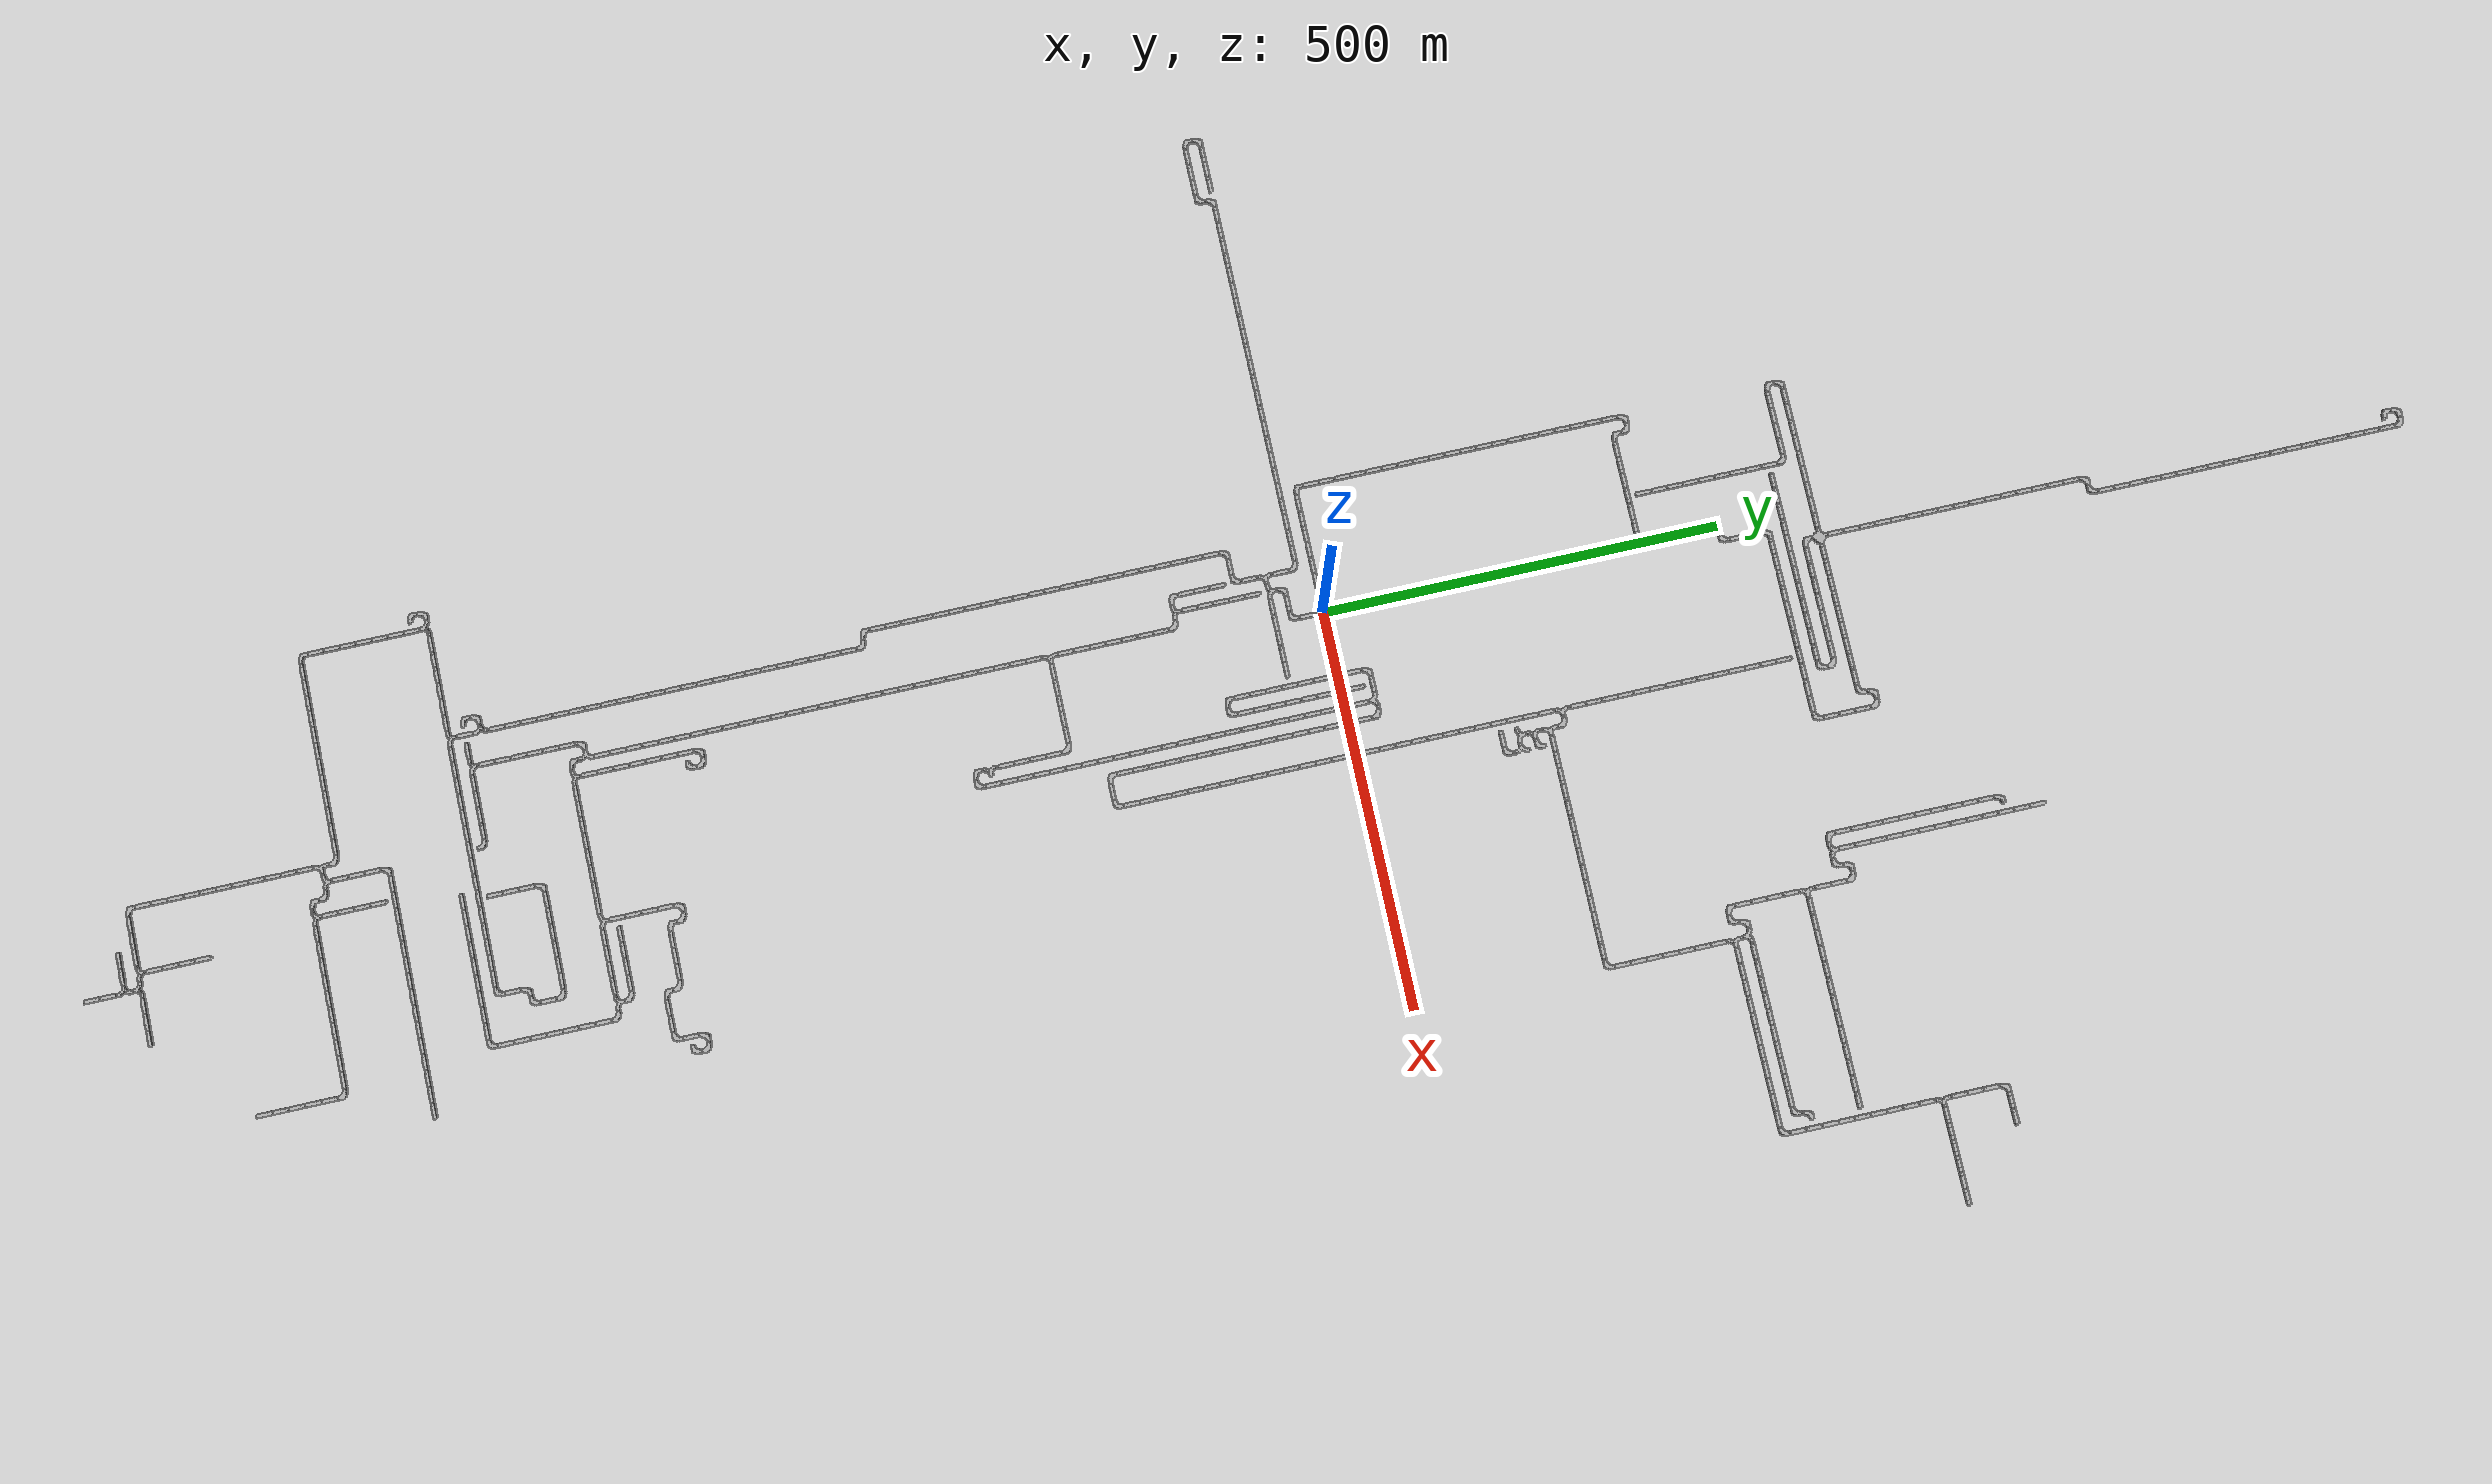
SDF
<sdf version="1.6">
<world name="cave_16000_0">
<include>
    <static>true</static>
    <name>cave_0_0</name>
    <pose>0 0 0 0 0 -1.5707963267948966</pose>
    <uri>model://cave_4way_20m</uri>
  </include>
  <include>
    <static>true</static>
    <name>cave_1_0</name>
    <pose>20 0 0 0 0 1.5707963267948966</pose>
    <uri>model://cave_straight_20m</uri>
  </include>
  <include>
    <static>true</static>
    <name>cave_2_0</name>
    <pose>40 0 0 0 0 1.5707963267948966</pose>
    <uri>model://cave_straight_20m</uri>
  </include>
  <include>
    <static>true</static>
    <name>cave_3_0</name>
    <pose>60 0 0 0 0 1.5707963267948966</pose>
    <uri>model://cave_straight_20m</uri>
  </include>
  <include>
    <static>true</static>
    <name>cave_4_0</name>
    <pose>80 0 0 0 0 1.5707963267948966</pose>
    <uri>model://cave_3way_20m</uri>
  </include>
  <include>
    <static>true</static>
    <name>cave_4_-1</name>
    <pose>80 -20 0 0 0 0.0</pose>
    <uri>model://cave_straight_20m</uri>
  </include>
  <include>
    <static>true</static>
    <name>cave_4_-2</name>
    <pose>80 -40 0 0 0 0.0</pose>
    <uri>model://cave_straight_20m</uri>
  </include>
  <include>
    <static>true</static>
    <name>cave_4_-3</name>
    <pose>80 -60 0 0 0 0.0</pose>
    <uri>model://cave_straight_20m</uri>
  </include>
  <include>
    <static>true</static>
    <name>cave_4_-4</name>
    <pose>80 -80 0 0 0 0.0</pose>
    <uri>model://cave_straight_20m</uri>
  </include>
  <include>
    <static>true</static>
    <name>cave_4_-5</name>
    <pose>80 -100 0 0 0 0.0</pose>
    <uri>model://cave_straight_20m</uri>
  </include>
  <include>
    <static>true</static>
    <name>cave_4_-6</name>
    <pose>80 -120 0 0 0 0.0</pose>
    <uri>model://cave_straight_20m</uri>
  </include>
  <include>
    <static>true</static>
    <name>cave_4_-7</name>
    <pose>80 -140 0 0 0 0.0</pose>
    <uri>model://cave_L_20m</uri>
  </include>
  <include>
    <static>true</static>
    <name>cave_5_-7</name>
    <pose>100 -140 0 0 0 1.5707963267948966</pose>
    <uri>model://cave_L_20m</uri>
  </include>
  <include>
    <static>true</static>
    <name>cave_5_-6</name>
    <pose>100 -120 0 0 0 0.0</pose>
    <uri>model://cave_straight_20m</uri>
  </include>
  <include>
    <static>true</static>
    <name>cave_5_-5</name>
    <pose>100 -100 0 0 0 0.0</pose>
    <uri>model://cave_straight_20m</uri>
  </include>
  <include>
    <static>true</static>
    <name>cave_5_-4</name>
    <pose>100 -80 0 0 0 0.0</pose>
    <uri>model://cave_straight_20m</uri>
  </include>
  <include>
    <static>true</static>
    <name>cave_5_-3</name>
    <pose>100 -60 0 0 0 0.0</pose>
    <uri>model://cave_straight_20m</uri>
  </include>
  <include>
    <static>true</static>
    <name>cave_5_-2</name>
    <pose>100 -40 0 0 0 0.0</pose>
    <uri>model://cave_straight_20m</uri>
  </include>
  <include>
    <static>true</static>
    <name>cave_5_-1</name>
    <pose>100 -20 0 0 0 0.0</pose>
    <uri>model://cave_straight_20m</uri>
  </include>
  <include>
    <static>true</static>
    <name>cave_5_0</name>
    <pose>100 0 0 0 0 0.0</pose>
    <uri>model://cave_straight_20m</uri>
  </include>
  <include>
    <static>true</static>
    <name>cave_5_1</name>
    <pose>100 20 0 0 0 0.0</pose>
    <uri>model://cave_straight_20m</uri>
  </include>
  <include>
    <static>true</static>
    <name>cave_4_1</name>
    <pose>80 20 0 0 0 0.0</pose>
    <uri>model://cave_straight_20m</uri>
  </include>
  <include>
    <static>true</static>
    <name>cave_4_2</name>
    <pose>80 40 0 0 0 -1.5707963267948966</pose>
    <uri>model://cave_L_20m</uri>
  </include>
  <include>
    <static>true</static>
    <name>cave_5_2</name>
    <pose>100 40 0 0 0 1.5707963267948966</pose>
    <uri>model://cave_straight_20m</uri>
  </include>
  <include>
    <static>true</static>
    <name>cave_6_2</name>
    <pose>120 40 0 0 0 3.141592653589793</pose>
    <uri>model://cave_3way_20m</uri>
  </include>
  <include>
    <static>true</static>
    <name>cave_7_2</name>
    <pose>140 40 0 0 0 3.141592653589793</pose>
    <uri>model://cave_L_20m</uri>
  </include>
  <include>
    <static>true</static>
    <name>cave_7_1</name>
    <pose>140 20 0 0 0 0.0</pose>
    <uri>model://cave_straight_20m</uri>
  </include>
  <include>
    <static>true</static>
    <name>cave_7_0</name>
    <pose>140 0 0 0 0 0.0</pose>
    <uri>model://cave_straight_20m</uri>
  </include>
  <include>
    <static>true</static>
    <name>cave_7_-1</name>
    <pose>140 -20 0 0 0 0.0</pose>
    <uri>model://cave_straight_20m</uri>
  </include>
  <include>
    <static>true</static>
    <name>cave_7_-2</name>
    <pose>140 -40 0 0 0 0.0</pose>
    <uri>model://cave_straight_20m</uri>
  </include>
  <include>
    <static>true</static>
    <name>cave_7_-3</name>
    <pose>140 -60 0 0 0 0.0</pose>
    <uri>model://cave_straight_20m</uri>
  </include>
  <include>
    <static>true</static>
    <name>cave_7_-4</name>
    <pose>140 -80 0 0 0 0.0</pose>
    <uri>model://cave_straight_20m</uri>
  </include>
  <include>
    <static>true</static>
    <name>cave_7_-5</name>
    <pose>140 -100 0 0 0 0.0</pose>
    <uri>model://cave_straight_20m</uri>
  </include>
  <include>
    <static>true</static>
    <name>cave_7_-6</name>
    <pose>140 -120 0 0 0 0.0</pose>
    <uri>model://cave_straight_20m</uri>
  </include>
  <include>
    <static>true</static>
    <name>cave_7_-7</name>
    <pose>140 -140 0 0 0 0.0</pose>
    <uri>model://cave_straight_20m</uri>
  </include>
  <include>
    <static>true</static>
    <name>cave_7_-8</name>
    <pose>140 -160 0 0 0 0.0</pose>
    <uri>model://cave_straight_20m</uri>
  </include>
  <include>
    <static>true</static>
    <name>cave_7_-9</name>
    <pose>140 -180 0 0 0 0.0</pose>
    <uri>model://cave_straight_20m</uri>
  </include>
  <include>
    <static>true</static>
    <name>cave_7_-10</name>
    <pose>140 -200 0 0 0 0.0</pose>
    <uri>model://cave_straight_20m</uri>
  </include>
  <include>
    <static>true</static>
    <name>cave_7_-11</name>
    <pose>140 -220 0 0 0 0.0</pose>
    <uri>model://cave_straight_20m</uri>
  </include>
  <include>
    <static>true</static>
    <name>cave_7_-12</name>
    <pose>140 -240 0 0 0 0.0</pose>
    <uri>model://cave_straight_20m</uri>
  </include>
  <include>
    <static>true</static>
    <name>cave_7_-13</name>
    <pose>140 -260 0 0 0 0.0</pose>
    <uri>model://cave_straight_20m</uri>
  </include>
  <include>
    <static>true</static>
    <name>cave_7_-14</name>
    <pose>140 -280 0 0 0 0.0</pose>
    <uri>model://cave_straight_20m</uri>
  </include>
  <include>
    <static>true</static>
    <name>cave_7_-15</name>
    <pose>140 -300 0 0 0 0.0</pose>
    <uri>model://cave_L_20m</uri>
  </include>
  <include>
    <static>true</static>
    <name>cave_8_-15</name>
    <pose>160 -300 0 0 0 1.5707963267948966</pose>
    <uri>model://cave_straight_20m</uri>
  </include>
  <include>
    <static>true</static>
    <name>cave_9_-15</name>
    <pose>180 -300 0 0 0 1.5707963267948966</pose>
    <uri>model://cave_L_20m</uri>
  </include>
  <include>
    <static>true</static>
    <name>cave_9_-14</name>
    <pose>180 -280 0 0 0 0.0</pose>
    <uri>model://cave_straight_20m</uri>
  </include>
  <include>
    <static>true</static>
    <name>cave_9_-13</name>
    <pose>180 -260 0 0 0 0.0</pose>
    <uri>model://cave_straight_20m</uri>
  </include>
  <include>
    <static>true</static>
    <name>cave_9_-12</name>
    <pose>180 -240 0 0 0 0.0</pose>
    <uri>model://cave_straight_20m</uri>
  </include>
  <include>
    <static>true</static>
    <name>cave_9_-11</name>
    <pose>180 -220 0 0 0 0.0</pose>
    <uri>model://cave_straight_20m</uri>
  </include>
  <include>
    <static>true</static>
    <name>cave_9_-10</name>
    <pose>180 -200 0 0 0 0.0</pose>
    <uri>model://cave_straight_20m</uri>
  </include>
  <include>
    <static>true</static>
    <name>cave_9_-9</name>
    <pose>180 -180 0 0 0 0.0</pose>
    <uri>model://cave_straight_20m</uri>
  </include>
  <include>
    <static>true</static>
    <name>cave_9_-8</name>
    <pose>180 -160 0 0 0 0.0</pose>
    <uri>model://cave_straight_20m</uri>
  </include>
  <include>
    <static>true</static>
    <name>cave_9_-7</name>
    <pose>180 -140 0 0 0 0.0</pose>
    <uri>model://cave_straight_20m</uri>
  </include>
  <include>
    <static>true</static>
    <name>cave_9_-6</name>
    <pose>180 -120 0 0 0 0.0</pose>
    <uri>model://cave_straight_20m</uri>
  </include>
  <include>
    <static>true</static>
    <name>cave_9_-5</name>
    <pose>180 -100 0 0 0 0.0</pose>
    <uri>model://cave_straight_20m</uri>
  </include>
  <include>
    <static>true</static>
    <name>cave_9_-4</name>
    <pose>180 -80 0 0 0 0.0</pose>
    <uri>model://cave_straight_20m</uri>
  </include>
  <include>
    <static>true</static>
    <name>cave_9_-3</name>
    <pose>180 -60 0 0 0 0.0</pose>
    <uri>model://cave_straight_20m</uri>
  </include>
  <include>
    <static>true</static>
    <name>cave_9_-2</name>
    <pose>180 -40 0 0 0 0.0</pose>
    <uri>model://cave_straight_20m</uri>
  </include>
  <include>
    <static>true</static>
    <name>cave_9_-1</name>
    <pose>180 -20 0 0 0 0.0</pose>
    <uri>model://cave_straight_20m</uri>
  </include>
  <include>
    <static>true</static>
    <name>cave_9_0</name>
    <pose>180 0 0 0 0 0.0</pose>
    <uri>model://cave_straight_20m</uri>
  </include>
  <include>
    <static>true</static>
    <name>cave_9_1</name>
    <pose>180 20 0 0 0 0.0</pose>
    <uri>model://cave_straight_20m</uri>
  </include>
  <include>
    <static>true</static>
    <name>cave_9_2</name>
    <pose>180 40 0 0 0 0.0</pose>
    <uri>model://cave_straight_20m</uri>
  </include>
  <include>
    <static>true</static>
    <name>cave_9_3</name>
    <pose>180 60 0 0 0 0.0</pose>
    <uri>model://cave_straight_20m</uri>
  </include>
  <include>
    <static>true</static>
    <name>cave_9_4</name>
    <pose>180 80 0 0 0 0.0</pose>
    <uri>model://cave_straight_20m</uri>
  </include>
  <include>
    <static>true</static>
    <name>cave_9_5</name>
    <pose>180 100 0 0 0 0.0</pose>
    <uri>model://cave_straight_20m</uri>
  </include>
  <include>
    <static>true</static>
    <name>cave_9_6</name>
    <pose>180 120 0 0 0 0.0</pose>
    <uri>model://cave_straight_20m</uri>
  </include>
  <include>
    <static>true</static>
    <name>cave_9_7</name>
    <pose>180 140 0 0 0 0.0</pose>
    <uri>model://cave_straight_20m</uri>
  </include>
  <include>
    <static>true</static>
    <name>cave_9_8</name>
    <pose>180 160 0 0 0 0.0</pose>
    <uri>model://cave_straight_20m</uri>
  </include>
  <include>
    <static>true</static>
    <name>cave_9_9</name>
    <pose>180 180 0 0 0 0.0</pose>
    <uri>model://cave_straight_20m</uri>
  </include>
  <include>
    <static>true</static>
    <name>cave_9_10</name>
    <pose>180 200 0 0 0 0.0</pose>
    <uri>model://cave_straight_20m</uri>
  </include>
  <include>
    <static>true</static>
    <name>cave_9_11</name>
    <pose>180 220 0 0 0 0.0</pose>
    <uri>model://cave_straight_20m</uri>
  </include>
  <include>
    <static>true</static>
    <name>cave_9_12</name>
    <pose>180 240 0 0 0 0.0</pose>
    <uri>model://cave_straight_20m</uri>
  </include>
  <include>
    <static>true</static>
    <name>cave_9_13</name>
    <pose>180 260 0 0 0 -1.5707963267948966</pose>
    <uri>model://cave_3way_20m</uri>
  </include>
  <include>
    <static>true</static>
    <name>cave_10_13</name>
    <pose>200 260 0 0 0 3.141592653589793</pose>
    <uri>model://cave_L_20m</uri>
  </include>
  <include>
    <static>true</static>
    <name>cave_10_12</name>
    <pose>200 240 0 0 0 -1.5707963267948966</pose>
    <uri>model://cave_3way_20m</uri>
  </include>
  <include>
    <static>true</static>
    <name>cave_11_12</name>
    <pose>220 240 0 0 0 1.5707963267948966</pose>
    <uri>model://cave_straight_20m</uri>
  </include>
  <include>
    <static>true</static>
    <name>cave_12_12</name>
    <pose>240 240 0 0 0 1.5707963267948966</pose>
    <uri>model://cave_straight_20m</uri>
  </include>
  <include>
    <static>true</static>
    <name>cave_13_12</name>
    <pose>260 240 0 0 0 1.5707963267948966</pose>
    <uri>model://cave_straight_20m</uri>
  </include>
  <include>
    <static>true</static>
    <name>cave_14_12</name>
    <pose>280 240 0 0 0 1.5707963267948966</pose>
    <uri>model://cave_straight_20m</uri>
  </include>
  <include>
    <static>true</static>
    <name>cave_15_12</name>
    <pose>300 240 0 0 0 1.5707963267948966</pose>
    <uri>model://cave_straight_20m</uri>
  </include>
  <include>
    <static>true</static>
    <name>cave_16_12</name>
    <pose>320 240 0 0 0 1.5707963267948966</pose>
    <uri>model://cave_straight_20m</uri>
  </include>
  <include>
    <static>true</static>
    <name>cave_17_12</name>
    <pose>340 240 0 0 0 1.5707963267948966</pose>
    <uri>model://cave_straight_20m</uri>
  </include>
  <include>
    <static>true</static>
    <name>cave_18_12</name>
    <pose>360 240 0 0 0 1.5707963267948966</pose>
    <uri>model://cave_straight_20m</uri>
  </include>
  <include>
    <static>true</static>
    <name>cave_19_12</name>
    <pose>380 240 0 0 0 1.5707963267948966</pose>
    <uri>model://cave_straight_20m</uri>
  </include>
  <include>
    <static>true</static>
    <name>cave_20_12</name>
    <pose>400 240 0 0 0 1.5707963267948966</pose>
    <uri>model://cave_straight_20m</uri>
  </include>
  <include>
    <static>true</static>
    <name>cave_21_12</name>
    <pose>420 240 0 0 0 1.5707963267948966</pose>
    <uri>model://cave_straight_20m</uri>
  </include>
  <include>
    <static>true</static>
    <name>cave_22_12</name>
    <pose>440 240 0 0 0 1.5707963267948966</pose>
    <uri>model://cave_straight_20m</uri>
  </include>
  <include>
    <static>true</static>
    <name>cave_23_12</name>
    <pose>460 240 0 0 0 1.5707963267948966</pose>
    <uri>model://cave_straight_20m</uri>
  </include>
  <include>
    <static>true</static>
    <name>cave_24_12</name>
    <pose>480 240 0 0 0 1.5707963267948966</pose>
    <uri>model://cave_straight_20m</uri>
  </include>
  <include>
    <static>true</static>
    <name>cave_25_12</name>
    <pose>500 240 0 0 0 1.5707963267948966</pose>
    <uri>model://cave_L_20m</uri>
  </include>
  <include>
    <static>true</static>
    <name>cave_25_13</name>
    <pose>500 260 0 0 0 0.0</pose>
    <uri>model://cave_straight_20m</uri>
  </include>
  <include>
    <static>true</static>
    <name>cave_25_14</name>
    <pose>500 280 0 0 0 0.0</pose>
    <uri>model://cave_straight_20m</uri>
  </include>
  <include>
    <static>true</static>
    <name>cave_25_15</name>
    <pose>500 300 0 0 0 0.0</pose>
    <uri>model://cave_straight_20m</uri>
  </include>
  <include>
    <static>true</static>
    <name>cave_25_16</name>
    <pose>500 320 0 0 0 0.0</pose>
    <uri>model://cave_straight_20m</uri>
  </include>
  <include>
    <static>true</static>
    <name>cave_25_17</name>
    <pose>500 340 0 0 0 0.0</pose>
    <uri>model://cave_straight_20m</uri>
  </include>
  <include>
    <static>true</static>
    <name>cave_25_18</name>
    <pose>500 360 0 0 0 0.0</pose>
    <uri>model://cave_straight_20m</uri>
  </include>
  <include>
    <static>true</static>
    <name>cave_25_19</name>
    <pose>500 380 0 0 0 0.0</pose>
    <uri>model://cave_straight_20m</uri>
  </include>
  <include>
    <static>true</static>
    <name>cave_25_20</name>
    <pose>500 400 0 0 0 -1.5707963267948966</pose>
    <uri>model://cave_3way_20m</uri>
  </include>
  <include>
    <static>true</static>
    <name>cave_26_20</name>
    <pose>520 400 0 0 0 1.5707963267948966</pose>
    <uri>model://cave_straight_20m</uri>
  </include>
  <include>
    <static>true</static>
    <name>cave_27_20</name>
    <pose>540 400 0 0 0 1.5707963267948966</pose>
    <uri>model://cave_straight_20m</uri>
  </include>
  <include>
    <static>true</static>
    <name>cave_28_20</name>
    <pose>560 400 0 0 0 1.5707963267948966</pose>
    <uri>model://cave_straight_20m</uri>
  </include>
  <include>
    <static>true</static>
    <name>cave_29_20</name>
    <pose>580 400 0 0 0 1.5707963267948966</pose>
    <uri>model://cave_straight_20m</uri>
  </include>
  <include>
    <static>true</static>
    <name>cave_30_20</name>
    <pose>600 400 0 0 0 1.5707963267948966</pose>
    <uri>model://cave_straight_20m</uri>
  </include>
  <include>
    <static>true</static>
    <name>cave_31_20</name>
    <pose>620 400 0 0 0 1.5707963267948966</pose>
    <uri>model://cave_straight_20m</uri>
  </include>
  <include>
    <static>true</static>
    <name>cave_32_20</name>
    <pose>640 400 0 0 0 1.5707963267948966</pose>
    <uri>model://cave_straight_20m</uri>
  </include>
  <include>
    <static>true</static>
    <name>cave_33_20</name>
    <pose>660 400 0 0 0 1.5707963267948966</pose>
    <uri>model://cave_straight_20m</uri>
  </include>
  <include>
    <static>true</static>
    <name>cave_34_20</name>
    <pose>680 400 0 0 0 1.5707963267948966</pose>
    <uri>model://cave_straight_20m</uri>
  </include>
  <include>
    <static>true</static>
    <name>cave_35_20</name>
    <pose>700 400 0 0 0 1.5707963267948966</pose>
    <uri>model://cave_straight_20m</uri>
  </include>
  <include>
    <static>true</static>
    <name>cave_36_20</name>
    <pose>720 400 0 0 0 1.5707963267948966</pose>
    <uri>model://cave_straight_20m</uri>
  </include>
  <include>
    <static>true</static>
    <name>cave_37_20</name>
    <pose>740 400 0 0 0 1.5707963267948966</pose>
    <uri>model://cave_L_20m</uri>
  </include>
  <include>
    <static>true</static>
    <name>cave_37_21</name>
    <pose>740 420 0 0 0 0.0</pose>
    <uri>model://cave_straight_20m</uri>
  </include>
  <include>
    <static>true</static>
    <name>cave_37_22</name>
    <pose>740 440 0 0 0 0.0</pose>
    <uri>model://cave_straight_20m</uri>
  </include>
  <include>
    <static>true</static>
    <name>cave_37_23</name>
    <pose>740 460 0 0 0 0.0</pose>
    <uri>model://cave_straight_20m</uri>
  </include>
  <include>
    <static>true</static>
    <name>cave_37_24</name>
    <pose>740 480 0 0 0 0.0</pose>
    <uri>model://cave_straight_20m</uri>
  </include>
  <include>
    <static>true</static>
    <name>cave_37_25</name>
    <pose>740 500 0 0 0 0.0</pose>
    <uri>model://cave_straight_20m</uri>
  </include>
  <include>
    <static>true</static>
    <name>cave_37_26</name>
    <pose>740 520 0 0 0 0.0</pose>
    <uri>model://cave_straight_20m</uri>
  </include>
  <include>
    <static>true</static>
    <name>cave_37_27</name>
    <pose>740 540 0 0 0 0.0</pose>
    <uri>model://cave_straight_20m</uri>
  </include>
  <include>
    <static>true</static>
    <name>cave_37_28</name>
    <pose>740 560 0 0 0 0.0</pose>
    <uri>model://cave_straight_20m</uri>
  </include>
  <include>
    <static>true</static>
    <name>cave_37_29</name>
    <pose>740 580 0 0 0 0.0</pose>
    <uri>model://cave_straight_20m</uri>
  </include>
  <include>
    <static>true</static>
    <name>cave_37_30</name>
    <pose>740 600 0 0 0 -1.5707963267948966</pose>
    <uri>model://cave_3way_20m</uri>
  </include>
  <include>
    <static>true</static>
    <name>cave_38_30</name>
    <pose>760 600 0 0 0 1.5707963267948966</pose>
    <uri>model://cave_straight_20m</uri>
  </include>
  <include>
    <static>true</static>
    <name>cave_39_30</name>
    <pose>780 600 0 0 0 1.5707963267948966</pose>
    <uri>model://cave_straight_20m</uri>
  </include>
  <include>
    <static>true</static>
    <name>cave_40_30</name>
    <pose>800 600 0 0 0 1.5707963267948966</pose>
    <uri>model://cave_straight_20m</uri>
  </include>
  <include>
    <static>true</static>
    <name>cave_41_30</name>
    <pose>820 600 0 0 0 1.5707963267948966</pose>
    <uri>model://cave_straight_20m</uri>
  </include>
  <include>
    <static>true</static>
    <name>cave_42_30</name>
    <pose>840 600 0 0 0 1.5707963267948966</pose>
    <uri>model://cave_straight_20m</uri>
  </include>
  <include>
    <static>true</static>
    <name>cave_43_30</name>
    <pose>860 600 0 0 0 1.5707963267948966</pose>
    <uri>model://cave_straight_20m</uri>
  </include>
  <include>
    <static>true</static>
    <name>cave_37_31</name>
    <pose>740 620 0 0 0 0.0</pose>
    <uri>model://cave_straight_20m</uri>
  </include>
  <include>
    <static>true</static>
    <name>cave_37_32</name>
    <pose>740 640 0 0 0 0.0</pose>
    <uri>model://cave_straight_20m</uri>
  </include>
  <include>
    <static>true</static>
    <name>cave_37_33</name>
    <pose>740 660 0 0 0 0.0</pose>
    <uri>model://cave_straight_20m</uri>
  </include>
  <include>
    <static>true</static>
    <name>cave_37_34</name>
    <pose>740 680 0 0 0 -1.5707963267948966</pose>
    <uri>model://cave_L_20m</uri>
  </include>
  <include>
    <static>true</static>
    <name>cave_38_34</name>
    <pose>760 680 0 0 0 1.5707963267948966</pose>
    <uri>model://cave_straight_20m</uri>
  </include>
  <include>
    <static>true</static>
    <name>cave_39_34</name>
    <pose>780 680 0 0 0 1.5707963267948966</pose>
    <uri>model://cave_straight_20m</uri>
  </include>
  <include>
    <static>true</static>
    <name>cave_25_21</name>
    <pose>500 420 0 0 0 3.141592653589793</pose>
    <uri>model://cave_3way_20m</uri>
  </include>
  <include>
    <static>true</static>
    <name>cave_26_21</name>
    <pose>520 420 0 0 0 1.5707963267948966</pose>
    <uri>model://cave_straight_20m</uri>
  </include>
  <include>
    <static>true</static>
    <name>cave_27_21</name>
    <pose>540 420 0 0 0 1.5707963267948966</pose>
    <uri>model://cave_straight_20m</uri>
  </include>
  <include>
    <static>true</static>
    <name>cave_28_21</name>
    <pose>560 420 0 0 0 1.5707963267948966</pose>
    <uri>model://cave_straight_20m</uri>
  </include>
  <include>
    <static>true</static>
    <name>cave_29_21</name>
    <pose>580 420 0 0 0 1.5707963267948966</pose>
    <uri>model://cave_straight_20m</uri>
  </include>
  <include>
    <static>true</static>
    <name>cave_30_21</name>
    <pose>600 420 0 0 0 1.5707963267948966</pose>
    <uri>model://cave_straight_20m</uri>
  </include>
  <include>
    <static>true</static>
    <name>cave_31_21</name>
    <pose>620 420 0 0 0 1.5707963267948966</pose>
    <uri>model://cave_straight_20m</uri>
  </include>
  <include>
    <static>true</static>
    <name>cave_32_21</name>
    <pose>640 420 0 0 0 1.5707963267948966</pose>
    <uri>model://cave_straight_20m</uri>
  </include>
  <include>
    <static>true</static>
    <name>cave_33_21</name>
    <pose>660 420 0 0 0 1.5707963267948966</pose>
    <uri>model://cave_straight_20m</uri>
  </include>
  <include>
    <static>true</static>
    <name>cave_34_21</name>
    <pose>680 420 0 0 0 1.5707963267948966</pose>
    <uri>model://cave_straight_20m</uri>
  </include>
  <include>
    <static>true</static>
    <name>cave_35_21</name>
    <pose>700 420 0 0 0 1.5707963267948966</pose>
    <uri>model://cave_straight_20m</uri>
  </include>
  <include>
    <static>true</static>
    <name>cave_36_21</name>
    <pose>720 420 0 0 0 1.5707963267948966</pose>
    <uri>model://cave_L_20m</uri>
  </include>
  <include>
    <static>true</static>
    <name>cave_36_22</name>
    <pose>720 440 0 0 0 -1.5707963267948966</pose>
    <uri>model://cave_L_20m</uri>
  </include>
  <include>
    <static>true</static>
    <name>cave_24_21</name>
    <pose>480 420 0 0 0 -1.5707963267948966</pose>
    <uri>model://cave_L_20m</uri>
  </include>
  <include>
    <static>true</static>
    <name>cave_24_20</name>
    <pose>480 400 0 0 0 1.5707963267948966</pose>
    <uri>model://cave_L_20m</uri>
  </include>
  <include>
    <static>true</static>
    <name>cave_23_20</name>
    <pose>460 400 0 0 0 0.0</pose>
    <uri>model://cave_L_20m</uri>
  </include>
  <include>
    <static>true</static>
    <name>cave_23_21</name>
    <pose>460 420 0 0 0 0.0</pose>
    <uri>model://cave_straight_20m</uri>
  </include>
  <include>
    <static>true</static>
    <name>cave_23_22</name>
    <pose>460 440 0 0 0 0.0</pose>
    <uri>model://cave_straight_20m</uri>
  </include>
  <include>
    <static>true</static>
    <name>cave_23_23</name>
    <pose>460 460 0 0 0 0.0</pose>
    <uri>model://cave_straight_20m</uri>
  </include>
  <include>
    <static>true</static>
    <name>cave_23_24</name>
    <pose>460 480 0 0 0 0.0</pose>
    <uri>model://cave_straight_20m</uri>
  </include>
  <include>
    <static>true</static>
    <name>cave_23_25</name>
    <pose>460 500 0 0 0 -1.5707963267948966</pose>
    <uri>model://cave_3way_20m</uri>
  </include>
  <include>
    <static>true</static>
    <name>cave_24_25</name>
    <pose>480 500 0 0 0 1.5707963267948966</pose>
    <uri>model://cave_straight_20m</uri>
  </include>
  <include>
    <static>true</static>
    <name>cave_25_25</name>
    <pose>500 500 0 0 0 1.5707963267948966</pose>
    <uri>model://cave_straight_20m</uri>
  </include>
  <include>
    <static>true</static>
    <name>cave_26_25</name>
    <pose>520 500 0 0 0 1.5707963267948966</pose>
    <uri>model://cave_straight_20m</uri>
  </include>
  <include>
    <static>true</static>
    <name>cave_27_25</name>
    <pose>540 500 0 0 0 1.5707963267948966</pose>
    <uri>model://cave_straight_20m</uri>
  </include>
  <include>
    <static>true</static>
    <name>cave_28_25</name>
    <pose>560 500 0 0 0 1.5707963267948966</pose>
    <uri>model://cave_straight_20m</uri>
  </include>
  <include>
    <static>true</static>
    <name>cave_29_25</name>
    <pose>580 500 0 0 0 1.5707963267948966</pose>
    <uri>model://cave_straight_20m</uri>
  </include>
  <include>
    <static>true</static>
    <name>cave_30_25</name>
    <pose>600 500 0 0 0 1.5707963267948966</pose>
    <uri>model://cave_straight_20m</uri>
  </include>
  <include>
    <static>true</static>
    <name>cave_31_25</name>
    <pose>620 500 0 0 0 1.5707963267948966</pose>
    <uri>model://cave_straight_20m</uri>
  </include>
  <include>
    <static>true</static>
    <name>cave_32_25</name>
    <pose>640 500 0 0 0 1.5707963267948966</pose>
    <uri>model://cave_straight_20m</uri>
  </include>
  <include>
    <static>true</static>
    <name>cave_33_25</name>
    <pose>660 500 0 0 0 1.5707963267948966</pose>
    <uri>model://cave_straight_20m</uri>
  </include>
  <include>
    <static>true</static>
    <name>cave_34_25</name>
    <pose>680 500 0 0 0 1.5707963267948966</pose>
    <uri>model://cave_straight_20m</uri>
  </include>
  <include>
    <static>true</static>
    <name>cave_35_25</name>
    <pose>700 500 0 0 0 1.5707963267948966</pose>
    <uri>model://cave_straight_20m</uri>
  </include>
  <include>
    <static>true</static>
    <name>cave_36_25</name>
    <pose>720 500 0 0 0 1.5707963267948966</pose>
    <uri>model://cave_straight_20m</uri>
  </include>
  <include>
    <static>true</static>
    <name>cave_23_26</name>
    <pose>460 520 0 0 0 0.0</pose>
    <uri>model://cave_straight_20m</uri>
  </include>
  <include>
    <static>true</static>
    <name>cave_23_27</name>
    <pose>460 540 0 0 0 0.0</pose>
    <uri>model://cave_straight_20m</uri>
  </include>
  <include>
    <static>true</static>
    <name>cave_23_28</name>
    <pose>460 560 0 0 0 3.141592653589793</pose>
    <uri>model://cave_L_20m</uri>
  </include>
  <include>
    <static>true</static>
    <name>cave_22_28</name>
    <pose>440 560 0 0 0 -1.5707963267948966</pose>
    <uri>model://cave_L_20m</uri>
  </include>
  <include>
    <static>true</static>
    <name>cave_22_27</name>
    <pose>440 540 0 0 0 1.5707963267948966</pose>
    <uri>model://cave_L_20m</uri>
  </include>
  <include>
    <static>true</static>
    <name>cave_21_27</name>
    <pose>420 540 0 0 0 0.0</pose>
    <uri>model://cave_3way_20m</uri>
  </include>
  <include>
    <static>true</static>
    <name>cave_20_27</name>
    <pose>400 540 0 0 0 0.0</pose>
    <uri>model://cave_L_20m</uri>
  </include>
  <include>
    <static>true</static>
    <name>cave_20_28</name>
    <pose>400 560 0 0 0 0.0</pose>
    <uri>model://cave_straight_20m</uri>
  </include>
  <include>
    <static>true</static>
    <name>cave_20_29</name>
    <pose>400 580 0 0 0 0.0</pose>
    <uri>model://cave_straight_20m</uri>
  </include>
  <include>
    <static>true</static>
    <name>cave_20_30</name>
    <pose>400 600 0 0 0 0.0</pose>
    <uri>model://cave_straight_20m</uri>
  </include>
  <include>
    <static>true</static>
    <name>cave_20_31</name>
    <pose>400 620 0 0 0 0.0</pose>
    <uri>model://cave_straight_20m</uri>
  </include>
  <include>
    <static>true</static>
    <name>cave_20_32</name>
    <pose>400 640 0 0 0 0.0</pose>
    <uri>model://cave_straight_20m</uri>
  </include>
  <include>
    <static>true</static>
    <name>cave_20_33</name>
    <pose>400 660 0 0 0 0.0</pose>
    <uri>model://cave_straight_20m</uri>
  </include>
  <include>
    <static>true</static>
    <name>cave_20_34</name>
    <pose>400 680 0 0 0 0.0</pose>
    <uri>model://cave_straight_20m</uri>
  </include>
  <include>
    <static>true</static>
    <name>cave_20_35</name>
    <pose>400 700 0 0 0 0.0</pose>
    <uri>model://cave_straight_20m</uri>
  </include>
  <include>
    <static>true</static>
    <name>cave_20_36</name>
    <pose>400 720 0 0 0 0.0</pose>
    <uri>model://cave_straight_20m</uri>
  </include>
  <include>
    <static>true</static>
    <name>cave_20_37</name>
    <pose>400 740 0 0 0 0.0</pose>
    <uri>model://cave_straight_20m</uri>
  </include>
  <include>
    <static>true</static>
    <name>cave_20_38</name>
    <pose>400 760 0 0 0 -1.5707963267948966</pose>
    <uri>model://cave_L_20m</uri>
  </include>
  <include>
    <static>true</static>
    <name>cave_21_28</name>
    <pose>420 560 0 0 0 0.0</pose>
    <uri>model://cave_straight_20m</uri>
  </include>
  <include>
    <static>true</static>
    <name>cave_21_29</name>
    <pose>420 580 0 0 0 0.0</pose>
    <uri>model://cave_straight_20m</uri>
  </include>
  <include>
    <static>true</static>
    <name>cave_21_30</name>
    <pose>420 600 0 0 0 0.0</pose>
    <uri>model://cave_straight_20m</uri>
  </include>
  <include>
    <static>true</static>
    <name>cave_21_31</name>
    <pose>420 620 0 0 0 0.0</pose>
    <uri>model://cave_straight_20m</uri>
  </include>
  <include>
    <static>true</static>
    <name>cave_21_32</name>
    <pose>420 640 0 0 0 0.0</pose>
    <uri>model://cave_straight_20m</uri>
  </include>
  <include>
    <static>true</static>
    <name>cave_21_33</name>
    <pose>420 660 0 0 0 0.0</pose>
    <uri>model://cave_straight_20m</uri>
  </include>
  <include>
    <static>true</static>
    <name>cave_21_34</name>
    <pose>420 680 0 0 0 0.0</pose>
    <uri>model://cave_straight_20m</uri>
  </include>
  <include>
    <static>true</static>
    <name>cave_21_35</name>
    <pose>420 700 0 0 0 0.0</pose>
    <uri>model://cave_straight_20m</uri>
  </include>
  <include>
    <static>true</static>
    <name>cave_21_36</name>
    <pose>420 720 0 0 0 0.0</pose>
    <uri>model://cave_straight_20m</uri>
  </include>
  <include>
    <static>true</static>
    <name>cave_21_37</name>
    <pose>420 740 0 0 0 0.0</pose>
    <uri>model://cave_straight_20m</uri>
  </include>
  <include>
    <static>true</static>
    <name>cave_21_38</name>
    <pose>420 760 0 0 0 0.0</pose>
    <uri>model://cave_straight_20m</uri>
  </include>
  <include>
    <static>true</static>
    <name>cave_21_39</name>
    <pose>420 780 0 0 0 0.0</pose>
    <uri>model://cave_straight_20m</uri>
  </include>
  <include>
    <static>true</static>
    <name>cave_21_40</name>
    <pose>420 800 0 0 0 0.0</pose>
    <uri>model://cave_straight_20m</uri>
  </include>
  <include>
    <static>true</static>
    <name>cave_10_11</name>
    <pose>200 220 0 0 0 -1.5707963267948966</pose>
    <uri>model://cave_3way_20m</uri>
  </include>
  <include>
    <static>true</static>
    <name>cave_11_11</name>
    <pose>220 220 0 0 0 1.5707963267948966</pose>
    <uri>model://cave_L_20m</uri>
  </include>
  <include>
    <static>true</static>
    <name>cave_10_10</name>
    <pose>200 200 0 0 0 0.0</pose>
    <uri>model://cave_3way_20m</uri>
  </include>
  <include>
    <static>true</static>
    <name>cave_11_10</name>
    <pose>220 200 0 0 0 1.5707963267948966</pose>
    <uri>model://cave_3way_20m</uri>
  </include>
  <include>
    <static>true</static>
    <name>cave_11_9</name>
    <pose>220 180 0 0 0 1.5707963267948966</pose>
    <uri>model://cave_L_20m</uri>
  </include>
  <include>
    <static>true</static>
    <name>cave_10_9</name>
    <pose>200 180 0 0 0 1.5707963267948966</pose>
    <uri>model://cave_straight_20m</uri>
  </include>
  <include>
    <static>true</static>
    <name>cave_9_14</name>
    <pose>180 280 0 0 0 0.0</pose>
    <uri>model://cave_straight_20m</uri>
  </include>
  <include>
    <static>true</static>
    <name>cave_9_15</name>
    <pose>180 300 0 0 0 0.0</pose>
    <uri>model://cave_straight_20m</uri>
  </include>
  <include>
    <static>true</static>
    <name>cave_9_16</name>
    <pose>180 320 0 0 0 0.0</pose>
    <uri>model://cave_straight_20m</uri>
  </include>
  <include>
    <static>true</static>
    <name>cave_9_17</name>
    <pose>180 340 0 0 0 0.0</pose>
    <uri>model://cave_straight_20m</uri>
  </include>
  <include>
    <static>true</static>
    <name>cave_9_18</name>
    <pose>180 360 0 0 0 0.0</pose>
    <uri>model://cave_straight_20m</uri>
  </include>
  <include>
    <static>true</static>
    <name>cave_9_19</name>
    <pose>180 380 0 0 0 0.0</pose>
    <uri>model://cave_straight_20m</uri>
  </include>
  <include>
    <static>true</static>
    <name>cave_9_20</name>
    <pose>180 400 0 0 0 0.0</pose>
    <uri>model://cave_straight_20m</uri>
  </include>
  <include>
    <static>true</static>
    <name>cave_9_21</name>
    <pose>180 420 0 0 0 0.0</pose>
    <uri>model://cave_straight_20m</uri>
  </include>
  <include>
    <static>true</static>
    <name>cave_9_22</name>
    <pose>180 440 0 0 0 0.0</pose>
    <uri>model://cave_straight_20m</uri>
  </include>
  <include>
    <static>true</static>
    <name>cave_9_23</name>
    <pose>180 460 0 0 0 0.0</pose>
    <uri>model://cave_straight_20m</uri>
  </include>
  <include>
    <static>true</static>
    <name>cave_9_24</name>
    <pose>180 480 0 0 0 0.0</pose>
    <uri>model://cave_straight_20m</uri>
  </include>
  <include>
    <static>true</static>
    <name>cave_9_25</name>
    <pose>180 500 0 0 0 0.0</pose>
    <uri>model://cave_straight_20m</uri>
  </include>
  <include>
    <static>true</static>
    <name>cave_9_26</name>
    <pose>180 520 0 0 0 0.0</pose>
    <uri>model://cave_straight_20m</uri>
  </include>
  <include>
    <static>true</static>
    <name>cave_9_27</name>
    <pose>180 540 0 0 0 0.0</pose>
    <uri>model://cave_straight_20m</uri>
  </include>
  <include>
    <static>true</static>
    <name>cave_6_1</name>
    <pose>120 20 0 0 0 0.0</pose>
    <uri>model://cave_straight_20m</uri>
  </include>
  <include>
    <static>true</static>
    <name>cave_6_0</name>
    <pose>120 0 0 0 0 0.0</pose>
    <uri>model://cave_straight_20m</uri>
  </include>
  <include>
    <static>true</static>
    <name>cave_6_-1</name>
    <pose>120 -20 0 0 0 0.0</pose>
    <uri>model://cave_straight_20m</uri>
  </include>
  <include>
    <static>true</static>
    <name>cave_6_-2</name>
    <pose>120 -40 0 0 0 0.0</pose>
    <uri>model://cave_straight_20m</uri>
  </include>
  <include>
    <static>true</static>
    <name>cave_6_-3</name>
    <pose>120 -60 0 0 0 0.0</pose>
    <uri>model://cave_straight_20m</uri>
  </include>
  <include>
    <static>true</static>
    <name>cave_6_-4</name>
    <pose>120 -80 0 0 0 0.0</pose>
    <uri>model://cave_straight_20m</uri>
  </include>
  <include>
    <static>true</static>
    <name>cave_6_-5</name>
    <pose>120 -100 0 0 0 0.0</pose>
    <uri>model://cave_straight_20m</uri>
  </include>
  <include>
    <static>true</static>
    <name>cave_6_-6</name>
    <pose>120 -120 0 0 0 0.0</pose>
    <uri>model://cave_straight_20m</uri>
  </include>
  <include>
    <static>true</static>
    <name>cave_6_-7</name>
    <pose>120 -140 0 0 0 0.0</pose>
    <uri>model://cave_straight_20m</uri>
  </include>
  <include>
    <static>true</static>
    <name>cave_6_-8</name>
    <pose>120 -160 0 0 0 0.0</pose>
    <uri>model://cave_straight_20m</uri>
  </include>
  <include>
    <static>true</static>
    <name>cave_6_-9</name>
    <pose>120 -180 0 0 0 0.0</pose>
    <uri>model://cave_straight_20m</uri>
  </include>
  <include>
    <static>true</static>
    <name>cave_6_-10</name>
    <pose>120 -200 0 0 0 0.0</pose>
    <uri>model://cave_straight_20m</uri>
  </include>
  <include>
    <static>true</static>
    <name>cave_6_-11</name>
    <pose>120 -220 0 0 0 0.0</pose>
    <uri>model://cave_straight_20m</uri>
  </include>
  <include>
    <static>true</static>
    <name>cave_6_-12</name>
    <pose>120 -240 0 0 0 0.0</pose>
    <uri>model://cave_straight_20m</uri>
  </include>
  <include>
    <static>true</static>
    <name>cave_6_-13</name>
    <pose>120 -260 0 0 0 0.0</pose>
    <uri>model://cave_straight_20m</uri>
  </include>
  <include>
    <static>true</static>
    <name>cave_6_-14</name>
    <pose>120 -280 0 0 0 0.0</pose>
    <uri>model://cave_straight_20m</uri>
  </include>
  <include>
    <static>true</static>
    <name>cave_6_-15</name>
    <pose>120 -300 0 0 0 0.0</pose>
    <uri>model://cave_straight_20m</uri>
  </include>
  <include>
    <static>true</static>
    <name>cave_6_-16</name>
    <pose>120 -320 0 0 0 0.0</pose>
    <uri>model://cave_straight_20m</uri>
  </include>
  <include>
    <static>true</static>
    <name>cave_6_-17</name>
    <pose>120 -340 0 0 0 0.0</pose>
    <uri>model://cave_straight_20m</uri>
  </include>
  <include>
    <static>true</static>
    <name>cave_6_-18</name>
    <pose>120 -360 0 0 0 0.0</pose>
    <uri>model://cave_straight_20m</uri>
  </include>
  <include>
    <static>true</static>
    <name>cave_6_-19</name>
    <pose>120 -380 0 0 0 0.0</pose>
    <uri>model://cave_straight_20m</uri>
  </include>
  <include>
    <static>true</static>
    <name>cave_6_-20</name>
    <pose>120 -400 0 0 0 0.0</pose>
    <uri>model://cave_straight_20m</uri>
  </include>
  <include>
    <static>true</static>
    <name>cave_6_-21</name>
    <pose>120 -420 0 0 0 0.0</pose>
    <uri>model://cave_straight_20m</uri>
  </include>
  <include>
    <static>true</static>
    <name>cave_6_-22</name>
    <pose>120 -440 0 0 0 0.0</pose>
    <uri>model://cave_straight_20m</uri>
  </include>
  <include>
    <static>true</static>
    <name>cave_6_-23</name>
    <pose>120 -460 0 0 0 1.5707963267948966</pose>
    <uri>model://cave_L_20m</uri>
  </include>
  <include>
    <static>true</static>
    <name>cave_5_-23</name>
    <pose>100 -460 0 0 0 0.0</pose>
    <uri>model://cave_L_20m</uri>
  </include>
  <include>
    <static>true</static>
    <name>cave_5_-22</name>
    <pose>100 -440 0 0 0 -1.5707963267948966</pose>
    <uri>model://cave_3way_20m</uri>
  </include>
  <include>
    <static>true</static>
    <name>cave_5_-21</name>
    <pose>100 -420 0 0 0 0.0</pose>
    <uri>model://cave_straight_20m</uri>
  </include>
  <include>
    <static>true</static>
    <name>cave_5_-20</name>
    <pose>100 -400 0 0 0 0.0</pose>
    <uri>model://cave_straight_20m</uri>
  </include>
  <include>
    <static>true</static>
    <name>cave_5_-19</name>
    <pose>100 -380 0 0 0 0.0</pose>
    <uri>model://cave_straight_20m</uri>
  </include>
  <include>
    <static>true</static>
    <name>cave_5_-18</name>
    <pose>100 -360 0 0 0 0.0</pose>
    <uri>model://cave_straight_20m</uri>
  </include>
  <include>
    <static>true</static>
    <name>cave_5_-17</name>
    <pose>100 -340 0 0 0 3.141592653589793</pose>
    <uri>model://cave_L_20m</uri>
  </include>
  <include>
    <static>true</static>
    <name>cave_4_-17</name>
    <pose>80 -340 0 0 0 1.5707963267948966</pose>
    <uri>model://cave_straight_20m</uri>
  </include>
  <include>
    <static>true</static>
    <name>cave_3_-17</name>
    <pose>60 -340 0 0 0 1.5707963267948966</pose>
    <uri>model://cave_straight_20m</uri>
  </include>
  <include>
    <static>true</static>
    <name>cave_2_-17</name>
    <pose>40 -340 0 0 0 1.5707963267948966</pose>
    <uri>model://cave_straight_20m</uri>
  </include>
  <include>
    <static>true</static>
    <name>cave_1_-17</name>
    <pose>20 -340 0 0 0 1.5707963267948966</pose>
    <uri>model://cave_straight_20m</uri>
  </include>
  <include>
    <static>true</static>
    <name>cave_0_-17</name>
    <pose>0 -340 0 0 0 1.5707963267948966</pose>
    <uri>model://cave_straight_20m</uri>
  </include>
  <include>
    <static>true</static>
    <name>cave_-1_-17</name>
    <pose>-20 -340 0 0 0 -1.5707963267948966</pose>
    <uri>model://cave_3way_20m</uri>
  </include>
  <include>
    <static>true</static>
    <name>cave_-1_-18</name>
    <pose>-20 -360 0 0 0 0.0</pose>
    <uri>model://cave_straight_20m</uri>
  </include>
  <include>
    <static>true</static>
    <name>cave_-1_-19</name>
    <pose>-20 -380 0 0 0 0.0</pose>
    <uri>model://cave_straight_20m</uri>
  </include>
  <include>
    <static>true</static>
    <name>cave_-1_-20</name>
    <pose>-20 -400 0 0 0 0.0</pose>
    <uri>model://cave_straight_20m</uri>
  </include>
  <include>
    <static>true</static>
    <name>cave_-1_-21</name>
    <pose>-20 -420 0 0 0 0.0</pose>
    <uri>model://cave_straight_20m</uri>
  </include>
  <include>
    <static>true</static>
    <name>cave_-1_-22</name>
    <pose>-20 -440 0 0 0 0.0</pose>
    <uri>model://cave_straight_20m</uri>
  </include>
  <include>
    <static>true</static>
    <name>cave_-1_-23</name>
    <pose>-20 -460 0 0 0 0.0</pose>
    <uri>model://cave_straight_20m</uri>
  </include>
  <include>
    <static>true</static>
    <name>cave_-1_-24</name>
    <pose>-20 -480 0 0 0 0.0</pose>
    <uri>model://cave_straight_20m</uri>
  </include>
  <include>
    <static>true</static>
    <name>cave_-1_-25</name>
    <pose>-20 -500 0 0 0 0.0</pose>
    <uri>model://cave_straight_20m</uri>
  </include>
  <include>
    <static>true</static>
    <name>cave_-1_-26</name>
    <pose>-20 -520 0 0 0 0.0</pose>
    <uri>model://cave_straight_20m</uri>
  </include>
  <include>
    <static>true</static>
    <name>cave_-1_-27</name>
    <pose>-20 -540 0 0 0 0.0</pose>
    <uri>model://cave_straight_20m</uri>
  </include>
  <include>
    <static>true</static>
    <name>cave_-1_-28</name>
    <pose>-20 -560 0 0 0 0.0</pose>
    <uri>model://cave_straight_20m</uri>
  </include>
  <include>
    <static>true</static>
    <name>cave_-1_-29</name>
    <pose>-20 -580 0 0 0 0.0</pose>
    <uri>model://cave_straight_20m</uri>
  </include>
  <include>
    <static>true</static>
    <name>cave_-1_-30</name>
    <pose>-20 -600 0 0 0 0.0</pose>
    <uri>model://cave_straight_20m</uri>
  </include>
  <include>
    <static>true</static>
    <name>cave_-1_-31</name>
    <pose>-20 -620 0 0 0 0.0</pose>
    <uri>model://cave_straight_20m</uri>
  </include>
  <include>
    <static>true</static>
    <name>cave_-1_-32</name>
    <pose>-20 -640 0 0 0 0.0</pose>
    <uri>model://cave_straight_20m</uri>
  </include>
  <include>
    <static>true</static>
    <name>cave_-1_-33</name>
    <pose>-20 -660 0 0 0 0.0</pose>
    <uri>model://cave_straight_20m</uri>
  </include>
  <include>
    <static>true</static>
    <name>cave_-1_-34</name>
    <pose>-20 -680 0 0 0 0.0</pose>
    <uri>model://cave_straight_20m</uri>
  </include>
  <include>
    <static>true</static>
    <name>cave_-1_-35</name>
    <pose>-20 -700 0 0 0 0.0</pose>
    <uri>model://cave_straight_20m</uri>
  </include>
  <include>
    <static>true</static>
    <name>cave_-1_-36</name>
    <pose>-20 -720 0 0 0 0.0</pose>
    <uri>model://cave_straight_20m</uri>
  </include>
  <include>
    <static>true</static>
    <name>cave_-1_-37</name>
    <pose>-20 -740 0 0 0 0.0</pose>
    <uri>model://cave_straight_20m</uri>
  </include>
  <include>
    <static>true</static>
    <name>cave_-1_-38</name>
    <pose>-20 -760 0 0 0 0.0</pose>
    <uri>model://cave_straight_20m</uri>
  </include>
  <include>
    <static>true</static>
    <name>cave_-1_-39</name>
    <pose>-20 -780 0 0 0 0.0</pose>
    <uri>model://cave_straight_20m</uri>
  </include>
  <include>
    <static>true</static>
    <name>cave_-1_-40</name>
    <pose>-20 -800 0 0 0 0.0</pose>
    <uri>model://cave_straight_20m</uri>
  </include>
  <include>
    <static>true</static>
    <name>cave_-1_-41</name>
    <pose>-20 -820 0 0 0 0.0</pose>
    <uri>model://cave_straight_20m</uri>
  </include>
  <include>
    <static>true</static>
    <name>cave_-1_-42</name>
    <pose>-20 -840 0 0 0 0.0</pose>
    <uri>model://cave_straight_20m</uri>
  </include>
  <include>
    <static>true</static>
    <name>cave_-1_-43</name>
    <pose>-20 -860 0 0 0 0.0</pose>
    <uri>model://cave_straight_20m</uri>
  </include>
  <include>
    <static>true</static>
    <name>cave_-1_-44</name>
    <pose>-20 -880 0 0 0 0.0</pose>
    <uri>model://cave_straight_20m</uri>
  </include>
  <include>
    <static>true</static>
    <name>cave_-1_-45</name>
    <pose>-20 -900 0 0 0 0.0</pose>
    <uri>model://cave_straight_20m</uri>
  </include>
  <include>
    <static>true</static>
    <name>cave_-1_-46</name>
    <pose>-20 -920 0 0 0 1.5707963267948966</pose>
    <uri>model://cave_3way_20m</uri>
  </include>
  <include>
    <static>true</static>
    <name>cave_-1_-47</name>
    <pose>-20 -940 0 0 0 0.0</pose>
    <uri>model://cave_L_20m</uri>
  </include>
  <include>
    <static>true</static>
    <name>cave_0_-47</name>
    <pose>0 -940 0 0 0 0.0</pose>
    <uri>model://cave_3way_20m</uri>
  </include>
  <include>
    <static>true</static>
    <name>cave_1_-47</name>
    <pose>20 -940 0 0 0 1.5707963267948966</pose>
    <uri>model://cave_straight_20m</uri>
  </include>
  <include>
    <static>true</static>
    <name>cave_2_-47</name>
    <pose>40 -940 0 0 0 1.5707963267948966</pose>
    <uri>model://cave_straight_20m</uri>
  </include>
  <include>
    <static>true</static>
    <name>cave_3_-47</name>
    <pose>60 -940 0 0 0 1.5707963267948966</pose>
    <uri>model://cave_straight_20m</uri>
  </include>
  <include>
    <static>true</static>
    <name>cave_4_-47</name>
    <pose>80 -940 0 0 0 1.5707963267948966</pose>
    <uri>model://cave_straight_20m</uri>
  </include>
  <include>
    <static>true</static>
    <name>cave_5_-47</name>
    <pose>100 -940 0 0 0 1.5707963267948966</pose>
    <uri>model://cave_straight_20m</uri>
  </include>
  <include>
    <static>true</static>
    <name>cave_6_-47</name>
    <pose>120 -940 0 0 0 1.5707963267948966</pose>
    <uri>model://cave_straight_20m</uri>
  </include>
  <include>
    <static>true</static>
    <name>cave_7_-47</name>
    <pose>140 -940 0 0 0 1.5707963267948966</pose>
    <uri>model://cave_straight_20m</uri>
  </include>
  <include>
    <static>true</static>
    <name>cave_8_-47</name>
    <pose>160 -940 0 0 0 1.5707963267948966</pose>
    <uri>model://cave_straight_20m</uri>
  </include>
  <include>
    <static>true</static>
    <name>cave_9_-47</name>
    <pose>180 -940 0 0 0 0.0</pose>
    <uri>model://cave_3way_20m</uri>
  </include>
  <include>
    <static>true</static>
    <name>cave_10_-47</name>
    <pose>200 -940 0 0 0 1.5707963267948966</pose>
    <uri>model://cave_straight_20m</uri>
  </include>
  <include>
    <static>true</static>
    <name>cave_11_-47</name>
    <pose>220 -940 0 0 0 1.5707963267948966</pose>
    <uri>model://cave_straight_20m</uri>
  </include>
  <include>
    <static>true</static>
    <name>cave_12_-47</name>
    <pose>240 -940 0 0 0 1.5707963267948966</pose>
    <uri>model://cave_straight_20m</uri>
  </include>
  <include>
    <static>true</static>
    <name>cave_13_-47</name>
    <pose>260 -940 0 0 0 1.5707963267948966</pose>
    <uri>model://cave_straight_20m</uri>
  </include>
  <include>
    <static>true</static>
    <name>cave_14_-47</name>
    <pose>280 -940 0 0 0 0.0</pose>
    <uri>model://cave_3way_20m</uri>
  </include>
  <include>
    <static>true</static>
    <name>cave_15_-47</name>
    <pose>300 -940 0 0 0 3.141592653589793</pose>
    <uri>model://cave_L_20m</uri>
  </include>
  <include>
    <static>true</static>
    <name>cave_15_-48</name>
    <pose>300 -960 0 0 0 0.0</pose>
    <uri>model://cave_straight_20m</uri>
  </include>
  <include>
    <static>true</static>
    <name>cave_15_-49</name>
    <pose>300 -980 0 0 0 0.0</pose>
    <uri>model://cave_straight_20m</uri>
  </include>
  <include>
    <static>true</static>
    <name>cave_15_-50</name>
    <pose>300 -1000 0 0 0 0.0</pose>
    <uri>model://cave_straight_20m</uri>
  </include>
  <include>
    <static>true</static>
    <name>cave_15_-51</name>
    <pose>300 -1020 0 0 0 0.0</pose>
    <uri>model://cave_straight_20m</uri>
  </include>
  <include>
    <static>true</static>
    <name>cave_15_-52</name>
    <pose>300 -1040 0 0 0 0.0</pose>
    <uri>model://cave_straight_20m</uri>
  </include>
  <include>
    <static>true</static>
    <name>cave_15_-53</name>
    <pose>300 -1060 0 0 0 0.0</pose>
    <uri>model://cave_straight_20m</uri>
  </include>
  <include>
    <static>true</static>
    <name>cave_15_-54</name>
    <pose>300 -1080 0 0 0 0.0</pose>
    <uri>model://cave_straight_20m</uri>
  </include>
  <include>
    <static>true</static>
    <name>cave_15_-55</name>
    <pose>300 -1100 0 0 0 1.5707963267948966</pose>
    <uri>model://cave_L_20m</uri>
  </include>
  <include>
    <static>true</static>
    <name>cave_14_-55</name>
    <pose>280 -1100 0 0 0 1.5707963267948966</pose>
    <uri>model://cave_straight_20m</uri>
  </include>
  <include>
    <static>true</static>
    <name>cave_13_-55</name>
    <pose>260 -1100 0 0 0 1.5707963267948966</pose>
    <uri>model://cave_straight_20m</uri>
  </include>
  <include>
    <static>true</static>
    <name>cave_12_-55</name>
    <pose>240 -1100 0 0 0 1.5707963267948966</pose>
    <uri>model://cave_straight_20m</uri>
  </include>
  <include>
    <static>true</static>
    <name>cave_11_-55</name>
    <pose>220 -1100 0 0 0 1.5707963267948966</pose>
    <uri>model://cave_straight_20m</uri>
  </include>
  <include>
    <static>true</static>
    <name>cave_10_-55</name>
    <pose>200 -1100 0 0 0 1.5707963267948966</pose>
    <uri>model://cave_straight_20m</uri>
  </include>
  <include>
    <static>true</static>
    <name>cave_9_-55</name>
    <pose>180 -1100 0 0 0 1.5707963267948966</pose>
    <uri>model://cave_straight_20m</uri>
  </include>
  <include>
    <static>true</static>
    <name>cave_8_-55</name>
    <pose>160 -1100 0 0 0 1.5707963267948966</pose>
    <uri>model://cave_straight_20m</uri>
  </include>
  <include>
    <static>true</static>
    <name>cave_7_-55</name>
    <pose>140 -1100 0 0 0 1.5707963267948966</pose>
    <uri>model://cave_straight_20m</uri>
  </include>
  <include>
    <static>true</static>
    <name>cave_6_-55</name>
    <pose>120 -1100 0 0 0 1.5707963267948966</pose>
    <uri>model://cave_straight_20m</uri>
  </include>
  <include>
    <static>true</static>
    <name>cave_14_-46</name>
    <pose>280 -920 0 0 0 3.141592653589793</pose>
    <uri>model://cave_L_20m</uri>
  </include>
  <include>
    <static>true</static>
    <name>cave_13_-46</name>
    <pose>260 -920 0 0 0 1.5707963267948966</pose>
    <uri>model://cave_straight_20m</uri>
  </include>
  <include>
    <static>true</static>
    <name>cave_12_-46</name>
    <pose>240 -920 0 0 0 1.5707963267948966</pose>
    <uri>model://cave_straight_20m</uri>
  </include>
  <include>
    <static>true</static>
    <name>cave_11_-46</name>
    <pose>220 -920 0 0 0 1.5707963267948966</pose>
    <uri>model://cave_straight_20m</uri>
  </include>
  <include>
    <static>true</static>
    <name>cave_10_-46</name>
    <pose>200 -920 0 0 0 1.5707963267948966</pose>
    <uri>model://cave_straight_20m</uri>
  </include>
  <include>
    <static>true</static>
    <name>cave_9_-46</name>
    <pose>180 -920 0 0 0 0.0</pose>
    <uri>model://cave_straight_20m</uri>
  </include>
  <include>
    <static>true</static>
    <name>cave_9_-45</name>
    <pose>180 -900 0 0 0 0.0</pose>
    <uri>model://cave_straight_20m</uri>
  </include>
  <include>
    <static>true</static>
    <name>cave_9_-44</name>
    <pose>180 -880 0 0 0 0.0</pose>
    <uri>model://cave_straight_20m</uri>
  </include>
  <include>
    <static>true</static>
    <name>cave_9_-43</name>
    <pose>180 -860 0 0 0 0.0</pose>
    <uri>model://cave_straight_20m</uri>
  </include>
  <include>
    <static>true</static>
    <name>cave_9_-42</name>
    <pose>180 -840 0 0 0 -1.5707963267948966</pose>
    <uri>model://cave_L_20m</uri>
  </include>
  <include>
    <static>true</static>
    <name>cave_10_-42</name>
    <pose>200 -840 0 0 0 3.141592653589793</pose>
    <uri>model://cave_L_20m</uri>
  </include>
  <include>
    <static>true</static>
    <name>cave_10_-43</name>
    <pose>200 -860 0 0 0 0.0</pose>
    <uri>model://cave_L_20m</uri>
  </include>
  <include>
    <static>true</static>
    <name>cave_11_-43</name>
    <pose>220 -860 0 0 0 1.5707963267948966</pose>
    <uri>model://cave_straight_20m</uri>
  </include>
  <include>
    <static>true</static>
    <name>cave_12_-43</name>
    <pose>240 -860 0 0 0 1.5707963267948966</pose>
    <uri>model://cave_straight_20m</uri>
  </include>
  <include>
    <static>true</static>
    <name>cave_13_-43</name>
    <pose>260 -860 0 0 0 1.5707963267948966</pose>
    <uri>model://cave_straight_20m</uri>
  </include>
  <include>
    <static>true</static>
    <name>cave_14_-43</name>
    <pose>280 -860 0 0 0 3.141592653589793</pose>
    <uri>model://cave_L_20m</uri>
  </include>
  <include>
    <static>true</static>
    <name>cave_14_-44</name>
    <pose>280 -880 0 0 0 0.0</pose>
    <uri>model://cave_L_20m</uri>
  </include>
  <include>
    <static>true</static>
    <name>cave_15_-44</name>
    <pose>300 -880 0 0 0 1.5707963267948966</pose>
    <uri>model://cave_straight_20m</uri>
  </include>
  <include>
    <static>true</static>
    <name>cave_16_-44</name>
    <pose>320 -880 0 0 0 1.5707963267948966</pose>
    <uri>model://cave_straight_20m</uri>
  </include>
  <include>
    <static>true</static>
    <name>cave_17_-44</name>
    <pose>340 -880 0 0 0 1.5707963267948966</pose>
    <uri>model://cave_L_20m</uri>
  </include>
  <include>
    <static>true</static>
    <name>cave_17_-43</name>
    <pose>340 -860 0 0 0 0.0</pose>
    <uri>model://cave_straight_20m</uri>
  </include>
  <include>
    <static>true</static>
    <name>cave_17_-42</name>
    <pose>340 -840 0 0 0 -1.5707963267948966</pose>
    <uri>model://cave_L_20m</uri>
  </include>
  <include>
    <static>true</static>
    <name>cave_18_-42</name>
    <pose>360 -840 0 0 0 3.141592653589793</pose>
    <uri>model://cave_L_20m</uri>
  </include>
  <include>
    <static>true</static>
    <name>cave_18_-43</name>
    <pose>360 -860 0 0 0 1.5707963267948966</pose>
    <uri>model://cave_L_20m</uri>
  </include>
  <include>
    <static>true</static>
    <name>cave_0_-46</name>
    <pose>0 -920 0 0 0 0.0</pose>
    <uri>model://cave_straight_20m</uri>
  </include>
  <include>
    <static>true</static>
    <name>cave_0_-45</name>
    <pose>0 -900 0 0 0 0.0</pose>
    <uri>model://cave_straight_20m</uri>
  </include>
  <include>
    <static>true</static>
    <name>cave_0_-44</name>
    <pose>0 -880 0 0 0 0.0</pose>
    <uri>model://cave_straight_20m</uri>
  </include>
  <include>
    <static>true</static>
    <name>cave_0_-43</name>
    <pose>0 -860 0 0 0 0.0</pose>
    <uri>model://cave_straight_20m</uri>
  </include>
  <include>
    <static>true</static>
    <name>cave_0_-42</name>
    <pose>0 -840 0 0 0 0.0</pose>
    <uri>model://cave_straight_20m</uri>
  </include>
  <include>
    <static>true</static>
    <name>cave_0_-41</name>
    <pose>0 -820 0 0 0 0.0</pose>
    <uri>model://cave_straight_20m</uri>
  </include>
  <include>
    <static>true</static>
    <name>cave_0_-40</name>
    <pose>0 -800 0 0 0 0.0</pose>
    <uri>model://cave_straight_20m</uri>
  </include>
  <include>
    <static>true</static>
    <name>cave_0_-39</name>
    <pose>0 -780 0 0 0 -1.5707963267948966</pose>
    <uri>model://cave_L_20m</uri>
  </include>
  <include>
    <static>true</static>
    <name>cave_1_-39</name>
    <pose>20 -780 0 0 0 3.141592653589793</pose>
    <uri>model://cave_L_20m</uri>
  </include>
  <include>
    <static>true</static>
    <name>cave_1_-40</name>
    <pose>20 -800 0 0 0 1.5707963267948966</pose>
    <uri>model://cave_L_20m</uri>
  </include>
  <include>
    <static>true</static>
    <name>cave_-2_-46</name>
    <pose>-40 -920 0 0 0 -1.5707963267948966</pose>
    <uri>model://cave_L_20m</uri>
  </include>
  <include>
    <static>true</static>
    <name>cave_-2_-47</name>
    <pose>-40 -940 0 0 0 0.0</pose>
    <uri>model://cave_straight_20m</uri>
  </include>
  <include>
    <static>true</static>
    <name>cave_-2_-48</name>
    <pose>-40 -960 0 0 0 0.0</pose>
    <uri>model://cave_straight_20m</uri>
  </include>
  <include>
    <static>true</static>
    <name>cave_-2_-49</name>
    <pose>-40 -980 0 0 0 0.0</pose>
    <uri>model://cave_straight_20m</uri>
  </include>
  <include>
    <static>true</static>
    <name>cave_-2_-50</name>
    <pose>-40 -1000 0 0 0 0.0</pose>
    <uri>model://cave_straight_20m</uri>
  </include>
  <include>
    <static>true</static>
    <name>cave_-2_-51</name>
    <pose>-40 -1020 0 0 0 0.0</pose>
    <uri>model://cave_straight_20m</uri>
  </include>
  <include>
    <static>true</static>
    <name>cave_-2_-52</name>
    <pose>-40 -1040 0 0 0 0.0</pose>
    <uri>model://cave_straight_20m</uri>
  </include>
  <include>
    <static>true</static>
    <name>cave_-2_-53</name>
    <pose>-40 -1060 0 0 0 0.0</pose>
    <uri>model://cave_3way_20m</uri>
  </include>
  <include>
    <static>true</static>
    <name>cave_-1_-53</name>
    <pose>-20 -1060 0 0 0 1.5707963267948966</pose>
    <uri>model://cave_straight_20m</uri>
  </include>
  <include>
    <static>true</static>
    <name>cave_0_-53</name>
    <pose>0 -1060 0 0 0 1.5707963267948966</pose>
    <uri>model://cave_straight_20m</uri>
  </include>
  <include>
    <static>true</static>
    <name>cave_1_-53</name>
    <pose>20 -1060 0 0 0 1.5707963267948966</pose>
    <uri>model://cave_straight_20m</uri>
  </include>
  <include>
    <static>true</static>
    <name>cave_2_-53</name>
    <pose>40 -1060 0 0 0 1.5707963267948966</pose>
    <uri>model://cave_straight_20m</uri>
  </include>
  <include>
    <static>true</static>
    <name>cave_3_-53</name>
    <pose>60 -1060 0 0 0 3.141592653589793</pose>
    <uri>model://cave_L_20m</uri>
  </include>
  <include>
    <static>true</static>
    <name>cave_-3_-53</name>
    <pose>-60 -1060 0 0 0 1.5707963267948966</pose>
    <uri>model://cave_straight_20m</uri>
  </include>
  <include>
    <static>true</static>
    <name>cave_-1_-16</name>
    <pose>-20 -320 0 0 0 0.0</pose>
    <uri>model://cave_straight_20m</uri>
  </include>
  <include>
    <static>true</static>
    <name>cave_-1_-15</name>
    <pose>-20 -300 0 0 0 0.0</pose>
    <uri>model://cave_straight_20m</uri>
  </include>
  <include>
    <static>true</static>
    <name>cave_-1_-14</name>
    <pose>-20 -280 0 0 0 0.0</pose>
    <uri>model://cave_straight_20m</uri>
  </include>
  <include>
    <static>true</static>
    <name>cave_-1_-13</name>
    <pose>-20 -260 0 0 0 0.0</pose>
    <uri>model://cave_straight_20m</uri>
  </include>
  <include>
    <static>true</static>
    <name>cave_-1_-12</name>
    <pose>-20 -240 0 0 0 0.0</pose>
    <uri>model://cave_straight_20m</uri>
  </include>
  <include>
    <static>true</static>
    <name>cave_-1_-11</name>
    <pose>-20 -220 0 0 0 0.0</pose>
    <uri>model://cave_straight_20m</uri>
  </include>
  <include>
    <static>true</static>
    <name>cave_-1_-10</name>
    <pose>-20 -200 0 0 0 0.0</pose>
    <uri>model://cave_straight_20m</uri>
  </include>
  <include>
    <static>true</static>
    <name>cave_-1_-9</name>
    <pose>-20 -180 0 0 0 3.141592653589793</pose>
    <uri>model://cave_L_20m</uri>
  </include>
  <include>
    <static>true</static>
    <name>cave_-2_-9</name>
    <pose>-40 -180 0 0 0 0.0</pose>
    <uri>model://cave_3way_20m</uri>
  </include>
  <include>
    <static>true</static>
    <name>cave_-3_-9</name>
    <pose>-60 -180 0 0 0 0.0</pose>
    <uri>model://cave_L_20m</uri>
  </include>
  <include>
    <static>true</static>
    <name>cave_-3_-8</name>
    <pose>-60 -160 0 0 0 0.0</pose>
    <uri>model://cave_straight_20m</uri>
  </include>
  <include>
    <static>true</static>
    <name>cave_-3_-7</name>
    <pose>-60 -140 0 0 0 0.0</pose>
    <uri>model://cave_straight_20m</uri>
  </include>
  <include>
    <static>true</static>
    <name>cave_-3_-6</name>
    <pose>-60 -120 0 0 0 0.0</pose>
    <uri>model://cave_straight_20m</uri>
  </include>
  <include>
    <static>true</static>
    <name>cave_-2_-8</name>
    <pose>-40 -160 0 0 0 0.0</pose>
    <uri>model://cave_straight_20m</uri>
  </include>
  <include>
    <static>true</static>
    <name>cave_-2_-7</name>
    <pose>-40 -140 0 0 0 0.0</pose>
    <uri>model://cave_straight_20m</uri>
  </include>
  <include>
    <static>true</static>
    <name>cave_-2_-6</name>
    <pose>-40 -120 0 0 0 0.0</pose>
    <uri>model://cave_straight_20m</uri>
  </include>
  <include>
    <static>true</static>
    <name>cave_-2_-5</name>
    <pose>-40 -100 0 0 0 0.0</pose>
    <uri>model://cave_straight_20m</uri>
  </include>
  <include>
    <static>true</static>
    <name>cave_-2_-4</name>
    <pose>-40 -80 0 0 0 0.0</pose>
    <uri>model://cave_straight_20m</uri>
  </include>
  <include>
    <static>true</static>
    <name>cave_0_-1</name>
    <pose>0 -20 0 0 0 0.0</pose>
    <uri>model://cave_straight_20m</uri>
  </include>
  <include>
    <static>true</static>
    <name>cave_0_-2</name>
    <pose>0 -40 0 0 0 1.5707963267948966</pose>
    <uri>model://cave_L_20m</uri>
  </include>
  <include>
    <static>true</static>
    <name>cave_-1_-2</name>
    <pose>-20 -40 0 0 0 1.5707963267948966</pose>
    <uri>model://cave_straight_20m</uri>
  </include>
  <include>
    <static>true</static>
    <name>cave_-2_-2</name>
    <pose>-40 -40 0 0 0 -1.5707963267948966</pose>
    <uri>model://cave_L_20m</uri>
  </include>
  <include>
    <static>true</static>
    <name>cave_-2_-3</name>
    <pose>-40 -60 0 0 0 0.0</pose>
    <uri>model://cave_3way_20m</uri>
  </include>
  <include>
    <static>true</static>
    <name>cave_-1_-3</name>
    <pose>-20 -60 0 0 0 1.5707963267948966</pose>
    <uri>model://cave_straight_20m</uri>
  </include>
  <include>
    <static>true</static>
    <name>cave_0_-3</name>
    <pose>0 -60 0 0 0 1.5707963267948966</pose>
    <uri>model://cave_straight_20m</uri>
  </include>
  <include>
    <static>true</static>
    <name>cave_1_-3</name>
    <pose>20 -60 0 0 0 1.5707963267948966</pose>
    <uri>model://cave_straight_20m</uri>
  </include>
  <include>
    <static>true</static>
    <name>cave_2_-3</name>
    <pose>40 -60 0 0 0 1.5707963267948966</pose>
    <uri>model://cave_straight_20m</uri>
  </include>
  <include>
    <static>true</static>
    <name>cave_3_-3</name>
    <pose>60 -60 0 0 0 1.5707963267948966</pose>
    <uri>model://cave_straight_20m</uri>
  </include>
  <include>
    <static>true</static>
    <name>cave_-3_-3</name>
    <pose>-60 -60 0 0 0 -1.5707963267948966</pose>
    <uri>model://cave_3way_20m</uri>
  </include>
  <include>
    <static>true</static>
    <name>cave_-3_-4</name>
    <pose>-60 -80 0 0 0 0.0</pose>
    <uri>model://cave_straight_20m</uri>
  </include>
  <include>
    <static>true</static>
    <name>cave_-3_-5</name>
    <pose>-60 -100 0 0 0 1.5707963267948966</pose>
    <uri>model://cave_L_20m</uri>
  </include>
  <include>
    <static>true</static>
    <name>cave_-4_-5</name>
    <pose>-80 -100 0 0 0 1.5707963267948966</pose>
    <uri>model://cave_straight_20m</uri>
  </include>
  <include>
    <static>true</static>
    <name>cave_-5_-5</name>
    <pose>-100 -100 0 0 0 -1.5707963267948966</pose>
    <uri>model://cave_L_20m</uri>
  </include>
  <include>
    <static>true</static>
    <name>cave_-5_-6</name>
    <pose>-100 -120 0 0 0 0.0</pose>
    <uri>model://cave_straight_20m</uri>
  </include>
  <include>
    <static>true</static>
    <name>cave_-5_-7</name>
    <pose>-100 -140 0 0 0 0.0</pose>
    <uri>model://cave_straight_20m</uri>
  </include>
  <include>
    <static>true</static>
    <name>cave_-5_-8</name>
    <pose>-100 -160 0 0 0 0.0</pose>
    <uri>model://cave_straight_20m</uri>
  </include>
  <include>
    <static>true</static>
    <name>cave_-5_-9</name>
    <pose>-100 -180 0 0 0 0.0</pose>
    <uri>model://cave_straight_20m</uri>
  </include>
  <include>
    <static>true</static>
    <name>cave_-5_-10</name>
    <pose>-100 -200 0 0 0 0.0</pose>
    <uri>model://cave_straight_20m</uri>
  </include>
  <include>
    <static>true</static>
    <name>cave_-5_-11</name>
    <pose>-100 -220 0 0 0 0.0</pose>
    <uri>model://cave_straight_20m</uri>
  </include>
  <include>
    <static>true</static>
    <name>cave_-5_-12</name>
    <pose>-100 -240 0 0 0 0.0</pose>
    <uri>model://cave_straight_20m</uri>
  </include>
  <include>
    <static>true</static>
    <name>cave_-5_-13</name>
    <pose>-100 -260 0 0 0 0.0</pose>
    <uri>model://cave_straight_20m</uri>
  </include>
  <include>
    <static>true</static>
    <name>cave_-5_-14</name>
    <pose>-100 -280 0 0 0 0.0</pose>
    <uri>model://cave_straight_20m</uri>
  </include>
  <include>
    <static>true</static>
    <name>cave_-5_-15</name>
    <pose>-100 -300 0 0 0 0.0</pose>
    <uri>model://cave_straight_20m</uri>
  </include>
  <include>
    <static>true</static>
    <name>cave_-5_-16</name>
    <pose>-100 -320 0 0 0 0.0</pose>
    <uri>model://cave_straight_20m</uri>
  </include>
  <include>
    <static>true</static>
    <name>cave_-5_-17</name>
    <pose>-100 -340 0 0 0 0.0</pose>
    <uri>model://cave_straight_20m</uri>
  </include>
  <include>
    <static>true</static>
    <name>cave_-5_-18</name>
    <pose>-100 -360 0 0 0 0.0</pose>
    <uri>model://cave_straight_20m</uri>
  </include>
  <include>
    <static>true</static>
    <name>cave_-5_-19</name>
    <pose>-100 -380 0 0 0 0.0</pose>
    <uri>model://cave_straight_20m</uri>
  </include>
  <include>
    <static>true</static>
    <name>cave_-5_-20</name>
    <pose>-100 -400 0 0 0 0.0</pose>
    <uri>model://cave_straight_20m</uri>
  </include>
  <include>
    <static>true</static>
    <name>cave_-5_-21</name>
    <pose>-100 -420 0 0 0 0.0</pose>
    <uri>model://cave_straight_20m</uri>
  </include>
  <include>
    <static>true</static>
    <name>cave_-5_-22</name>
    <pose>-100 -440 0 0 0 0.0</pose>
    <uri>model://cave_straight_20m</uri>
  </include>
  <include>
    <static>true</static>
    <name>cave_-5_-23</name>
    <pose>-100 -460 0 0 0 0.0</pose>
    <uri>model://cave_straight_20m</uri>
  </include>
  <include>
    <static>true</static>
    <name>cave_-5_-24</name>
    <pose>-100 -480 0 0 0 0.0</pose>
    <uri>model://cave_straight_20m</uri>
  </include>
  <include>
    <static>true</static>
    <name>cave_-5_-25</name>
    <pose>-100 -500 0 0 0 0.0</pose>
    <uri>model://cave_straight_20m</uri>
  </include>
  <include>
    <static>true</static>
    <name>cave_-5_-26</name>
    <pose>-100 -520 0 0 0 0.0</pose>
    <uri>model://cave_straight_20m</uri>
  </include>
  <include>
    <static>true</static>
    <name>cave_-5_-27</name>
    <pose>-100 -540 0 0 0 0.0</pose>
    <uri>model://cave_straight_20m</uri>
  </include>
  <include>
    <static>true</static>
    <name>cave_-5_-28</name>
    <pose>-100 -560 0 0 0 0.0</pose>
    <uri>model://cave_L_20m</uri>
  </include>
  <include>
    <static>true</static>
    <name>cave_-4_-28</name>
    <pose>-80 -560 0 0 0 3.141592653589793</pose>
    <uri>model://cave_L_20m</uri>
  </include>
  <include>
    <static>true</static>
    <name>cave_-4_-29</name>
    <pose>-80 -580 0 0 0 0.0</pose>
    <uri>model://cave_straight_20m</uri>
  </include>
  <include>
    <static>true</static>
    <name>cave_-4_-30</name>
    <pose>-80 -600 0 0 0 0.0</pose>
    <uri>model://cave_straight_20m</uri>
  </include>
  <include>
    <static>true</static>
    <name>cave_-4_-31</name>
    <pose>-80 -620 0 0 0 0.0</pose>
    <uri>model://cave_straight_20m</uri>
  </include>
  <include>
    <static>true</static>
    <name>cave_-4_-32</name>
    <pose>-80 -640 0 0 0 0.0</pose>
    <uri>model://cave_straight_20m</uri>
  </include>
  <include>
    <static>true</static>
    <name>cave_-4_-33</name>
    <pose>-80 -660 0 0 0 0.0</pose>
    <uri>model://cave_straight_20m</uri>
  </include>
  <include>
    <static>true</static>
    <name>cave_-4_-34</name>
    <pose>-80 -680 0 0 0 0.0</pose>
    <uri>model://cave_straight_20m</uri>
  </include>
  <include>
    <static>true</static>
    <name>cave_-4_-35</name>
    <pose>-80 -700 0 0 0 0.0</pose>
    <uri>model://cave_straight_20m</uri>
  </include>
  <include>
    <static>true</static>
    <name>cave_-4_-36</name>
    <pose>-80 -720 0 0 0 0.0</pose>
    <uri>model://cave_straight_20m</uri>
  </include>
  <include>
    <static>true</static>
    <name>cave_-4_-37</name>
    <pose>-80 -740 0 0 0 0.0</pose>
    <uri>model://cave_straight_20m</uri>
  </include>
  <include>
    <static>true</static>
    <name>cave_-4_-38</name>
    <pose>-80 -760 0 0 0 0.0</pose>
    <uri>model://cave_straight_20m</uri>
  </include>
  <include>
    <static>true</static>
    <name>cave_-4_-39</name>
    <pose>-80 -780 0 0 0 0.0</pose>
    <uri>model://cave_straight_20m</uri>
  </include>
  <include>
    <static>true</static>
    <name>cave_-4_-40</name>
    <pose>-80 -800 0 0 0 0.0</pose>
    <uri>model://cave_straight_20m</uri>
  </include>
  <include>
    <static>true</static>
    <name>cave_-4_-41</name>
    <pose>-80 -820 0 0 0 0.0</pose>
    <uri>model://cave_straight_20m</uri>
  </include>
  <include>
    <static>true</static>
    <name>cave_-4_-42</name>
    <pose>-80 -840 0 0 0 0.0</pose>
    <uri>model://cave_straight_20m</uri>
  </include>
  <include>
    <static>true</static>
    <name>cave_-4_-43</name>
    <pose>-80 -860 0 0 0 0.0</pose>
    <uri>model://cave_straight_20m</uri>
  </include>
  <include>
    <static>true</static>
    <name>cave_-4_-44</name>
    <pose>-80 -880 0 0 0 0.0</pose>
    <uri>model://cave_straight_20m</uri>
  </include>
  <include>
    <static>true</static>
    <name>cave_-4_-45</name>
    <pose>-80 -900 0 0 0 0.0</pose>
    <uri>model://cave_straight_20m</uri>
  </include>
  <include>
    <static>true</static>
    <name>cave_-4_-46</name>
    <pose>-80 -920 0 0 0 0.0</pose>
    <uri>model://cave_straight_20m</uri>
  </include>
  <include>
    <static>true</static>
    <name>cave_-4_-47</name>
    <pose>-80 -940 0 0 0 0.0</pose>
    <uri>model://cave_straight_20m</uri>
  </include>
  <include>
    <static>true</static>
    <name>cave_-4_-48</name>
    <pose>-80 -960 0 0 0 0.0</pose>
    <uri>model://cave_straight_20m</uri>
  </include>
  <include>
    <static>true</static>
    <name>cave_-4_-49</name>
    <pose>-80 -980 0 0 0 0.0</pose>
    <uri>model://cave_straight_20m</uri>
  </include>
  <include>
    <static>true</static>
    <name>cave_-4_-50</name>
    <pose>-80 -1000 0 0 0 0.0</pose>
    <uri>model://cave_straight_20m</uri>
  </include>
  <include>
    <static>true</static>
    <name>cave_-4_-51</name>
    <pose>-80 -1020 0 0 0 0.0</pose>
    <uri>model://cave_straight_20m</uri>
  </include>
  <include>
    <static>true</static>
    <name>cave_-4_-52</name>
    <pose>-80 -1040 0 0 0 1.5707963267948966</pose>
    <uri>model://cave_3way_20m</uri>
  </include>
  <include>
    <static>true</static>
    <name>cave_-4_-53</name>
    <pose>-80 -1060 0 0 0 0.0</pose>
    <uri>model://cave_straight_20m</uri>
  </include>
  <include>
    <static>true</static>
    <name>cave_-4_-54</name>
    <pose>-80 -1080 0 0 0 0.0</pose>
    <uri>model://cave_3way_20m</uri>
  </include>
  <include>
    <static>true</static>
    <name>cave_-3_-54</name>
    <pose>-60 -1080 0 0 0 1.5707963267948966</pose>
    <uri>model://cave_straight_20m</uri>
  </include>
  <include>
    <static>true</static>
    <name>cave_-2_-54</name>
    <pose>-40 -1080 0 0 0 1.5707963267948966</pose>
    <uri>model://cave_straight_20m</uri>
  </include>
  <include>
    <static>true</static>
    <name>cave_-1_-54</name>
    <pose>-20 -1080 0 0 0 1.5707963267948966</pose>
    <uri>model://cave_straight_20m</uri>
  </include>
  <include>
    <static>true</static>
    <name>cave_0_-54</name>
    <pose>0 -1080 0 0 0 1.5707963267948966</pose>
    <uri>model://cave_straight_20m</uri>
  </include>
  <include>
    <static>true</static>
    <name>cave_1_-54</name>
    <pose>20 -1080 0 0 0 1.5707963267948966</pose>
    <uri>model://cave_straight_20m</uri>
  </include>
  <include>
    <static>true</static>
    <name>cave_2_-54</name>
    <pose>40 -1080 0 0 0 1.5707963267948966</pose>
    <uri>model://cave_straight_20m</uri>
  </include>
  <include>
    <static>true</static>
    <name>cave_3_-54</name>
    <pose>60 -1080 0 0 0 1.5707963267948966</pose>
    <uri>model://cave_straight_20m</uri>
  </include>
  <include>
    <static>true</static>
    <name>cave_4_-54</name>
    <pose>80 -1080 0 0 0 1.5707963267948966</pose>
    <uri>model://cave_straight_20m</uri>
  </include>
  <include>
    <static>true</static>
    <name>cave_5_-54</name>
    <pose>100 -1080 0 0 0 1.5707963267948966</pose>
    <uri>model://cave_straight_20m</uri>
  </include>
  <include>
    <static>true</static>
    <name>cave_6_-54</name>
    <pose>120 -1080 0 0 0 1.5707963267948966</pose>
    <uri>model://cave_straight_20m</uri>
  </include>
  <include>
    <static>true</static>
    <name>cave_7_-54</name>
    <pose>140 -1080 0 0 0 1.5707963267948966</pose>
    <uri>model://cave_straight_20m</uri>
  </include>
  <include>
    <static>true</static>
    <name>cave_8_-54</name>
    <pose>160 -1080 0 0 0 1.5707963267948966</pose>
    <uri>model://cave_straight_20m</uri>
  </include>
  <include>
    <static>true</static>
    <name>cave_9_-54</name>
    <pose>180 -1080 0 0 0 1.5707963267948966</pose>
    <uri>model://cave_straight_20m</uri>
  </include>
  <include>
    <static>true</static>
    <name>cave_10_-54</name>
    <pose>200 -1080 0 0 0 1.5707963267948966</pose>
    <uri>model://cave_straight_20m</uri>
  </include>
  <include>
    <static>true</static>
    <name>cave_11_-54</name>
    <pose>220 -1080 0 0 0 1.5707963267948966</pose>
    <uri>model://cave_straight_20m</uri>
  </include>
  <include>
    <static>true</static>
    <name>cave_12_-54</name>
    <pose>240 -1080 0 0 0 1.5707963267948966</pose>
    <uri>model://cave_L_20m</uri>
  </include>
  <include>
    <static>true</static>
    <name>cave_12_-53</name>
    <pose>240 -1060 0 0 0 0.0</pose>
    <uri>model://cave_straight_20m</uri>
  </include>
  <include>
    <static>true</static>
    <name>cave_12_-52</name>
    <pose>240 -1040 0 0 0 -1.5707963267948966</pose>
    <uri>model://cave_L_20m</uri>
  </include>
  <include>
    <static>true</static>
    <name>cave_13_-52</name>
    <pose>260 -1040 0 0 0 1.5707963267948966</pose>
    <uri>model://cave_L_20m</uri>
  </include>
  <include>
    <static>true</static>
    <name>cave_13_-51</name>
    <pose>260 -1020 0 0 0 0.0</pose>
    <uri>model://cave_straight_20m</uri>
  </include>
  <include>
    <static>true</static>
    <name>cave_13_-50</name>
    <pose>260 -1000 0 0 0 3.141592653589793</pose>
    <uri>model://cave_L_20m</uri>
  </include>
  <include>
    <static>true</static>
    <name>cave_12_-50</name>
    <pose>240 -1000 0 0 0 1.5707963267948966</pose>
    <uri>model://cave_straight_20m</uri>
  </include>
  <include>
    <static>true</static>
    <name>cave_11_-50</name>
    <pose>220 -1000 0 0 0 1.5707963267948966</pose>
    <uri>model://cave_straight_20m</uri>
  </include>
  <include>
    <static>true</static>
    <name>cave_10_-50</name>
    <pose>200 -1000 0 0 0 1.5707963267948966</pose>
    <uri>model://cave_straight_20m</uri>
  </include>
  <include>
    <static>true</static>
    <name>cave_9_-50</name>
    <pose>180 -1000 0 0 0 1.5707963267948966</pose>
    <uri>model://cave_straight_20m</uri>
  </include>
  <include>
    <static>true</static>
    <name>cave_8_-50</name>
    <pose>160 -1000 0 0 0 1.5707963267948966</pose>
    <uri>model://cave_straight_20m</uri>
  </include>
  <include>
    <static>true</static>
    <name>cave_7_-50</name>
    <pose>140 -1000 0 0 0 1.5707963267948966</pose>
    <uri>model://cave_straight_20m</uri>
  </include>
  <include>
    <static>true</static>
    <name>cave_6_-50</name>
    <pose>120 -1000 0 0 0 -1.5707963267948966</pose>
    <uri>model://cave_L_20m</uri>
  </include>
  <include>
    <static>true</static>
    <name>cave_6_-51</name>
    <pose>120 -1020 0 0 0 0.0</pose>
    <uri>model://cave_straight_20m</uri>
  </include>
  <include>
    <static>true</static>
    <name>cave_6_-52</name>
    <pose>120 -1040 0 0 0 0.0</pose>
    <uri>model://cave_straight_20m</uri>
  </include>
  <include>
    <static>true</static>
    <name>cave_6_-53</name>
    <pose>120 -1060 0 0 0 0.0</pose>
    <uri>model://cave_straight_20m</uri>
  </include>
  <include>
    <static>true</static>
    <name>cave_-5_-54</name>
    <pose>-100 -1080 0 0 0 1.5707963267948966</pose>
    <uri>model://cave_straight_20m</uri>
  </include>
  <include>
    <static>true</static>
    <name>cave_-6_-54</name>
    <pose>-120 -1080 0 0 0 1.5707963267948966</pose>
    <uri>model://cave_straight_20m</uri>
  </include>
  <include>
    <static>true</static>
    <name>cave_-7_-54</name>
    <pose>-140 -1080 0 0 0 1.5707963267948966</pose>
    <uri>model://cave_straight_20m</uri>
  </include>
  <include>
    <static>true</static>
    <name>cave_-8_-54</name>
    <pose>-160 -1080 0 0 0 1.5707963267948966</pose>
    <uri>model://cave_straight_20m</uri>
  </include>
  <include>
    <static>true</static>
    <name>cave_-9_-54</name>
    <pose>-180 -1080 0 0 0 1.5707963267948966</pose>
    <uri>model://cave_straight_20m</uri>
  </include>
  <include>
    <static>true</static>
    <name>cave_-10_-54</name>
    <pose>-200 -1080 0 0 0 1.5707963267948966</pose>
    <uri>model://cave_straight_20m</uri>
  </include>
  <include>
    <static>true</static>
    <name>cave_-11_-54</name>
    <pose>-220 -1080 0 0 0 3.141592653589793</pose>
    <uri>model://cave_3way_20m</uri>
  </include>
  <include>
    <static>true</static>
    <name>cave_-11_-55</name>
    <pose>-220 -1100 0 0 0 0.0</pose>
    <uri>model://cave_straight_20m</uri>
  </include>
  <include>
    <static>true</static>
    <name>cave_-11_-56</name>
    <pose>-220 -1120 0 0 0 0.0</pose>
    <uri>model://cave_straight_20m</uri>
  </include>
  <include>
    <static>true</static>
    <name>cave_-11_-57</name>
    <pose>-220 -1140 0 0 0 0.0</pose>
    <uri>model://cave_straight_20m</uri>
  </include>
  <include>
    <static>true</static>
    <name>cave_-11_-58</name>
    <pose>-220 -1160 0 0 0 0.0</pose>
    <uri>model://cave_straight_20m</uri>
  </include>
  <include>
    <static>true</static>
    <name>cave_-11_-59</name>
    <pose>-220 -1180 0 0 0 0.0</pose>
    <uri>model://cave_straight_20m</uri>
  </include>
  <include>
    <static>true</static>
    <name>cave_-11_-60</name>
    <pose>-220 -1200 0 0 0 0.0</pose>
    <uri>model://cave_straight_20m</uri>
  </include>
  <include>
    <static>true</static>
    <name>cave_-11_-61</name>
    <pose>-220 -1220 0 0 0 0.0</pose>
    <uri>model://cave_straight_20m</uri>
  </include>
  <include>
    <static>true</static>
    <name>cave_-11_-62</name>
    <pose>-220 -1240 0 0 0 0.0</pose>
    <uri>model://cave_L_20m</uri>
  </include>
  <include>
    <static>true</static>
    <name>cave_-10_-62</name>
    <pose>-200 -1240 0 0 0 1.5707963267948966</pose>
    <uri>model://cave_straight_20m</uri>
  </include>
  <include>
    <static>true</static>
    <name>cave_-9_-62</name>
    <pose>-180 -1240 0 0 0 1.5707963267948966</pose>
    <uri>model://cave_straight_20m</uri>
  </include>
  <include>
    <static>true</static>
    <name>cave_-8_-62</name>
    <pose>-160 -1240 0 0 0 1.5707963267948966</pose>
    <uri>model://cave_straight_20m</uri>
  </include>
  <include>
    <static>true</static>
    <name>cave_-7_-62</name>
    <pose>-140 -1240 0 0 0 1.5707963267948966</pose>
    <uri>model://cave_straight_20m</uri>
  </include>
  <include>
    <static>true</static>
    <name>cave_-6_-62</name>
    <pose>-120 -1240 0 0 0 1.5707963267948966</pose>
    <uri>model://cave_straight_20m</uri>
  </include>
  <include>
    <static>true</static>
    <name>cave_-5_-62</name>
    <pose>-100 -1240 0 0 0 1.5707963267948966</pose>
    <uri>model://cave_straight_20m</uri>
  </include>
  <include>
    <static>true</static>
    <name>cave_-4_-62</name>
    <pose>-80 -1240 0 0 0 1.5707963267948966</pose>
    <uri>model://cave_straight_20m</uri>
  </include>
  <include>
    <static>true</static>
    <name>cave_-3_-62</name>
    <pose>-60 -1240 0 0 0 1.5707963267948966</pose>
    <uri>model://cave_straight_20m</uri>
  </include>
  <include>
    <static>true</static>
    <name>cave_-2_-62</name>
    <pose>-40 -1240 0 0 0 1.5707963267948966</pose>
    <uri>model://cave_straight_20m</uri>
  </include>
  <include>
    <static>true</static>
    <name>cave_-1_-62</name>
    <pose>-20 -1240 0 0 0 1.5707963267948966</pose>
    <uri>model://cave_straight_20m</uri>
  </include>
  <include>
    <static>true</static>
    <name>cave_0_-62</name>
    <pose>0 -1240 0 0 0 1.5707963267948966</pose>
    <uri>model://cave_straight_20m</uri>
  </include>
  <include>
    <static>true</static>
    <name>cave_1_-62</name>
    <pose>20 -1240 0 0 0 1.5707963267948966</pose>
    <uri>model://cave_straight_20m</uri>
  </include>
  <include>
    <static>true</static>
    <name>cave_2_-62</name>
    <pose>40 -1240 0 0 0 3.141592653589793</pose>
    <uri>model://cave_L_20m</uri>
  </include>
  <include>
    <static>true</static>
    <name>cave_2_-63</name>
    <pose>40 -1260 0 0 0 -1.5707963267948966</pose>
    <uri>model://cave_3way_20m</uri>
  </include>
  <include>
    <static>true</static>
    <name>cave_3_-63</name>
    <pose>60 -1260 0 0 0 0.0</pose>
    <uri>model://cave_3way_20m</uri>
  </include>
  <include>
    <static>true</static>
    <name>cave_4_-63</name>
    <pose>80 -1260 0 0 0 3.141592653589793</pose>
    <uri>model://cave_L_20m</uri>
  </include>
  <include>
    <static>true</static>
    <name>cave_4_-64</name>
    <pose>80 -1280 0 0 0 0.0</pose>
    <uri>model://cave_L_20m</uri>
  </include>
  <include>
    <static>true</static>
    <name>cave_5_-64</name>
    <pose>100 -1280 0 0 0 0.0</pose>
    <uri>model://cave_3way_20m</uri>
  </include>
  <include>
    <static>true</static>
    <name>cave_6_-64</name>
    <pose>120 -1280 0 0 0 1.5707963267948966</pose>
    <uri>model://cave_straight_20m</uri>
  </include>
  <include>
    <static>true</static>
    <name>cave_7_-64</name>
    <pose>140 -1280 0 0 0 1.5707963267948966</pose>
    <uri>model://cave_straight_20m</uri>
  </include>
  <include>
    <static>true</static>
    <name>cave_8_-64</name>
    <pose>160 -1280 0 0 0 1.5707963267948966</pose>
    <uri>model://cave_straight_20m</uri>
  </include>
  <include>
    <static>true</static>
    <name>cave_9_-64</name>
    <pose>180 -1280 0 0 0 1.5707963267948966</pose>
    <uri>model://cave_straight_20m</uri>
  </include>
  <include>
    <static>true</static>
    <name>cave_10_-64</name>
    <pose>200 -1280 0 0 0 1.5707963267948966</pose>
    <uri>model://cave_straight_20m</uri>
  </include>
  <include>
    <static>true</static>
    <name>cave_11_-64</name>
    <pose>220 -1280 0 0 0 1.5707963267948966</pose>
    <uri>model://cave_straight_20m</uri>
  </include>
  <include>
    <static>true</static>
    <name>cave_12_-64</name>
    <pose>240 -1280 0 0 0 1.5707963267948966</pose>
    <uri>model://cave_straight_20m</uri>
  </include>
  <include>
    <static>true</static>
    <name>cave_13_-64</name>
    <pose>260 -1280 0 0 0 1.5707963267948966</pose>
    <uri>model://cave_straight_20m</uri>
  </include>
  <include>
    <static>true</static>
    <name>cave_14_-64</name>
    <pose>280 -1280 0 0 0 1.5707963267948966</pose>
    <uri>model://cave_straight_20m</uri>
  </include>
  <include>
    <static>true</static>
    <name>cave_15_-64</name>
    <pose>300 -1280 0 0 0 1.5707963267948966</pose>
    <uri>model://cave_straight_20m</uri>
  </include>
  <include>
    <static>true</static>
    <name>cave_16_-64</name>
    <pose>320 -1280 0 0 0 3.141592653589793</pose>
    <uri>model://cave_L_20m</uri>
  </include>
  <include>
    <static>true</static>
    <name>cave_16_-65</name>
    <pose>320 -1300 0 0 0 0.0</pose>
    <uri>model://cave_straight_20m</uri>
  </include>
  <include>
    <static>true</static>
    <name>cave_16_-66</name>
    <pose>320 -1320 0 0 0 0.0</pose>
    <uri>model://cave_straight_20m</uri>
  </include>
  <include>
    <static>true</static>
    <name>cave_16_-67</name>
    <pose>320 -1340 0 0 0 0.0</pose>
    <uri>model://cave_straight_20m</uri>
  </include>
  <include>
    <static>true</static>
    <name>cave_16_-68</name>
    <pose>320 -1360 0 0 0 0.0</pose>
    <uri>model://cave_straight_20m</uri>
  </include>
  <include>
    <static>true</static>
    <name>cave_16_-69</name>
    <pose>320 -1380 0 0 0 0.0</pose>
    <uri>model://cave_straight_20m</uri>
  </include>
  <include>
    <static>true</static>
    <name>cave_5_-63</name>
    <pose>100 -1260 0 0 0 0.0</pose>
    <uri>model://cave_straight_20m</uri>
  </include>
  <include>
    <static>true</static>
    <name>cave_5_-62</name>
    <pose>100 -1240 0 0 0 0.0</pose>
    <uri>model://cave_straight_20m</uri>
  </include>
  <include>
    <static>true</static>
    <name>cave_5_-61</name>
    <pose>100 -1220 0 0 0 0.0</pose>
    <uri>model://cave_straight_20m</uri>
  </include>
  <include>
    <static>true</static>
    <name>cave_5_-60</name>
    <pose>100 -1200 0 0 0 0.0</pose>
    <uri>model://cave_straight_20m</uri>
  </include>
  <include>
    <static>true</static>
    <name>cave_3_-62</name>
    <pose>60 -1240 0 0 0 0.0</pose>
    <uri>model://cave_straight_20m</uri>
  </include>
  <include>
    <static>true</static>
    <name>cave_3_-61</name>
    <pose>60 -1220 0 0 0 0.0</pose>
    <uri>model://cave_straight_20m</uri>
  </include>
  <include>
    <static>true</static>
    <name>cave_3_-60</name>
    <pose>60 -1200 0 0 0 0.0</pose>
    <uri>model://cave_straight_20m</uri>
  </include>
  <include>
    <static>true</static>
    <name>cave_3_-59</name>
    <pose>60 -1180 0 0 0 -1.5707963267948966</pose>
    <uri>model://cave_L_20m</uri>
  </include>
  <include>
    <static>true</static>
    <name>cave_4_-59</name>
    <pose>80 -1180 0 0 0 1.5707963267948966</pose>
    <uri>model://cave_straight_20m</uri>
  </include>
  <include>
    <static>true</static>
    <name>cave_5_-59</name>
    <pose>100 -1180 0 0 0 1.5707963267948966</pose>
    <uri>model://cave_straight_20m</uri>
  </include>
  <include>
    <static>true</static>
    <name>cave_6_-59</name>
    <pose>120 -1180 0 0 0 1.5707963267948966</pose>
    <uri>model://cave_straight_20m</uri>
  </include>
  <include>
    <static>true</static>
    <name>cave_7_-59</name>
    <pose>140 -1180 0 0 0 1.5707963267948966</pose>
    <uri>model://cave_straight_20m</uri>
  </include>
  <include>
    <static>true</static>
    <name>cave_8_-59</name>
    <pose>160 -1180 0 0 0 1.5707963267948966</pose>
    <uri>model://cave_straight_20m</uri>
  </include>
  <include>
    <static>true</static>
    <name>cave_9_-59</name>
    <pose>180 -1180 0 0 0 1.5707963267948966</pose>
    <uri>model://cave_straight_20m</uri>
  </include>
  <include>
    <static>true</static>
    <name>cave_10_-59</name>
    <pose>200 -1180 0 0 0 1.5707963267948966</pose>
    <uri>model://cave_straight_20m</uri>
  </include>
  <include>
    <static>true</static>
    <name>cave_11_-59</name>
    <pose>220 -1180 0 0 0 1.5707963267948966</pose>
    <uri>model://cave_straight_20m</uri>
  </include>
  <include>
    <static>true</static>
    <name>cave_12_-59</name>
    <pose>240 -1180 0 0 0 1.5707963267948966</pose>
    <uri>model://cave_straight_20m</uri>
  </include>
  <include>
    <static>true</static>
    <name>cave_13_-59</name>
    <pose>260 -1180 0 0 0 1.5707963267948966</pose>
    <uri>model://cave_straight_20m</uri>
  </include>
  <include>
    <static>true</static>
    <name>cave_14_-59</name>
    <pose>280 -1180 0 0 0 1.5707963267948966</pose>
    <uri>model://cave_straight_20m</uri>
  </include>
  <include>
    <static>true</static>
    <name>cave_15_-59</name>
    <pose>300 -1180 0 0 0 1.5707963267948966</pose>
    <uri>model://cave_straight_20m</uri>
  </include>
  <include>
    <static>true</static>
    <name>cave_16_-59</name>
    <pose>320 -1180 0 0 0 1.5707963267948966</pose>
    <uri>model://cave_straight_20m</uri>
  </include>
  <include>
    <static>true</static>
    <name>cave_17_-59</name>
    <pose>340 -1180 0 0 0 1.5707963267948966</pose>
    <uri>model://cave_straight_20m</uri>
  </include>
  <include>
    <static>true</static>
    <name>cave_18_-59</name>
    <pose>360 -1180 0 0 0 1.5707963267948966</pose>
    <uri>model://cave_straight_20m</uri>
  </include>
  <include>
    <static>true</static>
    <name>cave_2_-64</name>
    <pose>40 -1280 0 0 0 0.0</pose>
    <uri>model://cave_straight_20m</uri>
  </include>
  <include>
    <static>true</static>
    <name>cave_2_-65</name>
    <pose>40 -1300 0 0 0 0.0</pose>
    <uri>model://cave_straight_20m</uri>
  </include>
  <include>
    <static>true</static>
    <name>cave_2_-66</name>
    <pose>40 -1320 0 0 0 0.0</pose>
    <uri>model://cave_straight_20m</uri>
  </include>
  <include>
    <static>true</static>
    <name>cave_2_-67</name>
    <pose>40 -1340 0 0 0 0.0</pose>
    <uri>model://cave_straight_20m</uri>
  </include>
  <include>
    <static>true</static>
    <name>cave_2_-68</name>
    <pose>40 -1360 0 0 0 0.0</pose>
    <uri>model://cave_straight_20m</uri>
  </include>
  <include>
    <static>true</static>
    <name>cave_2_-69</name>
    <pose>40 -1380 0 0 0 0.0</pose>
    <uri>model://cave_straight_20m</uri>
  </include>
  <include>
    <static>true</static>
    <name>cave_2_-70</name>
    <pose>40 -1400 0 0 0 0.0</pose>
    <uri>model://cave_straight_20m</uri>
  </include>
  <include>
    <static>true</static>
    <name>cave_2_-71</name>
    <pose>40 -1420 0 0 0 0.0</pose>
    <uri>model://cave_straight_20m</uri>
  </include>
  <include>
    <static>true</static>
    <name>cave_2_-72</name>
    <pose>40 -1440 0 0 0 0.0</pose>
    <uri>model://cave_straight_20m</uri>
  </include>
  <include>
    <static>true</static>
    <name>cave_2_-73</name>
    <pose>40 -1460 0 0 0 0.0</pose>
    <uri>model://cave_straight_20m</uri>
  </include>
  <include>
    <static>true</static>
    <name>cave_2_-74</name>
    <pose>40 -1480 0 0 0 0.0</pose>
    <uri>model://cave_straight_20m</uri>
  </include>
  <include>
    <static>true</static>
    <name>cave_2_-75</name>
    <pose>40 -1500 0 0 0 0.0</pose>
    <uri>model://cave_L_20m</uri>
  </include>
  <include>
    <static>true</static>
    <name>cave_3_-75</name>
    <pose>60 -1500 0 0 0 1.5707963267948966</pose>
    <uri>model://cave_straight_20m</uri>
  </include>
  <include>
    <static>true</static>
    <name>cave_4_-75</name>
    <pose>80 -1500 0 0 0 1.5707963267948966</pose>
    <uri>model://cave_straight_20m</uri>
  </include>
  <include>
    <static>true</static>
    <name>cave_5_-75</name>
    <pose>100 -1500 0 0 0 1.5707963267948966</pose>
    <uri>model://cave_straight_20m</uri>
  </include>
  <include>
    <static>true</static>
    <name>cave_6_-75</name>
    <pose>120 -1500 0 0 0 0.0</pose>
    <uri>model://cave_3way_20m</uri>
  </include>
  <include>
    <static>true</static>
    <name>cave_7_-75</name>
    <pose>140 -1500 0 0 0 3.141592653589793</pose>
    <uri>model://cave_3way_20m</uri>
  </include>
  <include>
    <static>true</static>
    <name>cave_8_-75</name>
    <pose>160 -1500 0 0 0 1.5707963267948966</pose>
    <uri>model://cave_straight_20m</uri>
  </include>
  <include>
    <static>true</static>
    <name>cave_9_-75</name>
    <pose>180 -1500 0 0 0 1.5707963267948966</pose>
    <uri>model://cave_straight_20m</uri>
  </include>
  <include>
    <static>true</static>
    <name>cave_10_-75</name>
    <pose>200 -1500 0 0 0 1.5707963267948966</pose>
    <uri>model://cave_straight_20m</uri>
  </include>
  <include>
    <static>true</static>
    <name>cave_7_-76</name>
    <pose>140 -1520 0 0 0 1.5707963267948966</pose>
    <uri>model://cave_3way_20m</uri>
  </include>
  <include>
    <static>true</static>
    <name>cave_7_-77</name>
    <pose>140 -1540 0 0 0 0.0</pose>
    <uri>model://cave_straight_20m</uri>
  </include>
  <include>
    <static>true</static>
    <name>cave_7_-78</name>
    <pose>140 -1560 0 0 0 0.0</pose>
    <uri>model://cave_straight_20m</uri>
  </include>
  <include>
    <static>true</static>
    <name>cave_6_-76</name>
    <pose>120 -1520 0 0 0 1.5707963267948966</pose>
    <uri>model://cave_straight_20m</uri>
  </include>
  <include>
    <static>true</static>
    <name>cave_5_-76</name>
    <pose>100 -1520 0 0 0 1.5707963267948966</pose>
    <uri>model://cave_straight_20m</uri>
  </include>
  <include>
    <static>true</static>
    <name>cave_6_-74</name>
    <pose>120 -1480 0 0 0 0.0</pose>
    <uri>model://cave_straight_20m</uri>
  </include>
  <include>
    <static>true</static>
    <name>cave_6_-73</name>
    <pose>120 -1460 0 0 0 0.0</pose>
    <uri>model://cave_straight_20m</uri>
  </include>
  <include>
    <static>true</static>
    <name>cave_6_-72</name>
    <pose>120 -1440 0 0 0 0.0</pose>
    <uri>model://cave_straight_20m</uri>
  </include>
  <include>
    <static>true</static>
    <name>cave_6_-71</name>
    <pose>120 -1420 0 0 0 0.0</pose>
    <uri>model://cave_straight_20m</uri>
  </include>
  <include>
    <static>true</static>
    <name>cave_-12_-54</name>
    <pose>-240 -1080 0 0 0 -1.5707963267948966</pose>
    <uri>model://cave_L_20m</uri>
  </include>
  <include>
    <static>true</static>
    <name>cave_-12_-55</name>
    <pose>-240 -1100 0 0 0 0.0</pose>
    <uri>model://cave_L_20m</uri>
  </include>
  <include>
    <static>true</static>
    <name>cave_-5_-52</name>
    <pose>-100 -1040 0 0 0 -1.5707963267948966</pose>
    <uri>model://cave_L_20m</uri>
  </include>
  <include>
    <static>true</static>
    <name>cave_-5_-53</name>
    <pose>-100 -1060 0 0 0 0.0</pose>
    <uri>model://cave_L_20m</uri>
  </include>
  <include>
    <static>true</static>
    <name>cave_-3_-2</name>
    <pose>-60 -40 0 0 0 0.0</pose>
    <uri>model://cave_straight_20m</uri>
  </include>
  <include>
    <static>true</static>
    <name>cave_-3_-1</name>
    <pose>-60 -20 0 0 0 3.141592653589793</pose>
    <uri>model://cave_L_20m</uri>
  </include>
  <include>
    <static>true</static>
    <name>cave_-4_-1</name>
    <pose>-80 -20 0 0 0 1.5707963267948966</pose>
    <uri>model://cave_straight_20m</uri>
  </include>
  <include>
    <static>true</static>
    <name>cave_-5_-1</name>
    <pose>-100 -20 0 0 0 1.5707963267948966</pose>
    <uri>model://cave_straight_20m</uri>
  </include>
  <include>
    <static>true</static>
    <name>cave_-6_-1</name>
    <pose>-120 -20 0 0 0 1.5707963267948966</pose>
    <uri>model://cave_straight_20m</uri>
  </include>
  <include>
    <static>true</static>
    <name>cave_-7_-1</name>
    <pose>-140 -20 0 0 0 1.5707963267948966</pose>
    <uri>model://cave_straight_20m</uri>
  </include>
  <include>
    <static>true</static>
    <name>cave_-8_-1</name>
    <pose>-160 -20 0 0 0 1.5707963267948966</pose>
    <uri>model://cave_straight_20m</uri>
  </include>
  <include>
    <static>true</static>
    <name>cave_-9_-1</name>
    <pose>-180 -20 0 0 0 1.5707963267948966</pose>
    <uri>model://cave_straight_20m</uri>
  </include>
  <include>
    <static>true</static>
    <name>cave_-10_-1</name>
    <pose>-200 -20 0 0 0 1.5707963267948966</pose>
    <uri>model://cave_straight_20m</uri>
  </include>
  <include>
    <static>true</static>
    <name>cave_-11_-1</name>
    <pose>-220 -20 0 0 0 1.5707963267948966</pose>
    <uri>model://cave_straight_20m</uri>
  </include>
  <include>
    <static>true</static>
    <name>cave_-12_-1</name>
    <pose>-240 -20 0 0 0 1.5707963267948966</pose>
    <uri>model://cave_straight_20m</uri>
  </include>
  <include>
    <static>true</static>
    <name>cave_-13_-1</name>
    <pose>-260 -20 0 0 0 1.5707963267948966</pose>
    <uri>model://cave_straight_20m</uri>
  </include>
  <include>
    <static>true</static>
    <name>cave_-14_-1</name>
    <pose>-280 -20 0 0 0 1.5707963267948966</pose>
    <uri>model://cave_straight_20m</uri>
  </include>
  <include>
    <static>true</static>
    <name>cave_-15_-1</name>
    <pose>-300 -20 0 0 0 1.5707963267948966</pose>
    <uri>model://cave_straight_20m</uri>
  </include>
  <include>
    <static>true</static>
    <name>cave_-16_-1</name>
    <pose>-320 -20 0 0 0 1.5707963267948966</pose>
    <uri>model://cave_straight_20m</uri>
  </include>
  <include>
    <static>true</static>
    <name>cave_-17_-1</name>
    <pose>-340 -20 0 0 0 1.5707963267948966</pose>
    <uri>model://cave_straight_20m</uri>
  </include>
  <include>
    <static>true</static>
    <name>cave_-18_-1</name>
    <pose>-360 -20 0 0 0 1.5707963267948966</pose>
    <uri>model://cave_straight_20m</uri>
  </include>
  <include>
    <static>true</static>
    <name>cave_-19_-1</name>
    <pose>-380 -20 0 0 0 1.5707963267948966</pose>
    <uri>model://cave_straight_20m</uri>
  </include>
  <include>
    <static>true</static>
    <name>cave_-20_-1</name>
    <pose>-400 -20 0 0 0 1.5707963267948966</pose>
    <uri>model://cave_straight_20m</uri>
  </include>
  <include>
    <static>true</static>
    <name>cave_-21_-1</name>
    <pose>-420 -20 0 0 0 1.5707963267948966</pose>
    <uri>model://cave_straight_20m</uri>
  </include>
  <include>
    <static>true</static>
    <name>cave_-22_-1</name>
    <pose>-440 -20 0 0 0 1.5707963267948966</pose>
    <uri>model://cave_straight_20m</uri>
  </include>
  <include>
    <static>true</static>
    <name>cave_-23_-1</name>
    <pose>-460 -20 0 0 0 1.5707963267948966</pose>
    <uri>model://cave_straight_20m</uri>
  </include>
  <include>
    <static>true</static>
    <name>cave_-24_-1</name>
    <pose>-480 -20 0 0 0 1.5707963267948966</pose>
    <uri>model://cave_straight_20m</uri>
  </include>
  <include>
    <static>true</static>
    <name>cave_-25_-1</name>
    <pose>-500 -20 0 0 0 1.5707963267948966</pose>
    <uri>model://cave_straight_20m</uri>
  </include>
  <include>
    <static>true</static>
    <name>cave_-26_-1</name>
    <pose>-520 -20 0 0 0 1.5707963267948966</pose>
    <uri>model://cave_straight_20m</uri>
  </include>
  <include>
    <static>true</static>
    <name>cave_-27_-1</name>
    <pose>-540 -20 0 0 0 -1.5707963267948966</pose>
    <uri>model://cave_L_20m</uri>
  </include>
  <include>
    <static>true</static>
    <name>cave_-27_-2</name>
    <pose>-540 -40 0 0 0 1.5707963267948966</pose>
    <uri>model://cave_L_20m</uri>
  </include>
  <include>
    <static>true</static>
    <name>cave_-28_-2</name>
    <pose>-560 -40 0 0 0 1.5707963267948966</pose>
    <uri>model://cave_straight_20m</uri>
  </include>
  <include>
    <static>true</static>
    <name>cave_-29_-2</name>
    <pose>-580 -40 0 0 0 1.5707963267948966</pose>
    <uri>model://cave_straight_20m</uri>
  </include>
  <include>
    <static>true</static>
    <name>cave_-30_-2</name>
    <pose>-600 -40 0 0 0 1.5707963267948966</pose>
    <uri>model://cave_straight_20m</uri>
  </include>
  <include>
    <static>true</static>
    <name>cave_-31_-2</name>
    <pose>-620 -40 0 0 0 0.0</pose>
    <uri>model://cave_L_20m</uri>
  </include>
  <include>
    <static>true</static>
    <name>cave_-31_-1</name>
    <pose>-620 -20 0 0 0 -1.5707963267948966</pose>
    <uri>model://cave_L_20m</uri>
  </include>
  <include>
    <static>true</static>
    <name>cave_-30_-1</name>
    <pose>-600 -20 0 0 0 1.5707963267948966</pose>
    <uri>model://cave_straight_20m</uri>
  </include>
  <include>
    <static>true</static>
    <name>cave_-29_-1</name>
    <pose>-580 -20 0 0 0 1.5707963267948966</pose>
    <uri>model://cave_straight_20m</uri>
  </include>
  <include>
    <static>true</static>
    <name>cave_-28_-1</name>
    <pose>-560 -20 0 0 0 1.5707963267948966</pose>
    <uri>model://cave_straight_20m</uri>
  </include>
  <include>
    <static>true</static>
    <name>cave_-1_0</name>
    <pose>-20 0 0 0 0 1.5707963267948966</pose>
    <uri>model://cave_straight_20m</uri>
  </include>
  <include>
    <static>true</static>
    <name>cave_-2_0</name>
    <pose>-40 0 0 0 0 1.5707963267948966</pose>
    <uri>model://cave_straight_20m</uri>
  </include>
  <include>
    <static>true</static>
    <name>cave_-3_0</name>
    <pose>-60 0 0 0 0 1.5707963267948966</pose>
    <uri>model://cave_straight_20m</uri>
  </include>
  <include>
    <static>true</static>
    <name>cave_-4_0</name>
    <pose>-80 0 0 0 0 1.5707963267948966</pose>
    <uri>model://cave_straight_20m</uri>
  </include>
  <include>
    <static>true</static>
    <name>cave_-5_0</name>
    <pose>-100 0 0 0 0 1.5707963267948966</pose>
    <uri>model://cave_straight_20m</uri>
  </include>
  <include>
    <static>true</static>
    <name>cave_-6_0</name>
    <pose>-120 0 0 0 0 1.5707963267948966</pose>
    <uri>model://cave_straight_20m</uri>
  </include>
  <include>
    <static>true</static>
    <name>cave_-7_0</name>
    <pose>-140 0 0 0 0 1.5707963267948966</pose>
    <uri>model://cave_straight_20m</uri>
  </include>
  <include>
    <static>true</static>
    <name>cave_-8_0</name>
    <pose>-160 0 0 0 0 0.0</pose>
    <uri>model://cave_L_20m</uri>
  </include>
  <include>
    <static>true</static>
    <name>cave_-8_1</name>
    <pose>-160 20 0 0 0 0.0</pose>
    <uri>model://cave_straight_20m</uri>
  </include>
  <include>
    <static>true</static>
    <name>cave_-8_2</name>
    <pose>-160 40 0 0 0 0.0</pose>
    <uri>model://cave_straight_20m</uri>
  </include>
  <include>
    <static>true</static>
    <name>cave_-8_3</name>
    <pose>-160 60 0 0 0 0.0</pose>
    <uri>model://cave_straight_20m</uri>
  </include>
  <include>
    <static>true</static>
    <name>cave_-8_4</name>
    <pose>-160 80 0 0 0 0.0</pose>
    <uri>model://cave_straight_20m</uri>
  </include>
  <include>
    <static>true</static>
    <name>cave_-8_5</name>
    <pose>-160 100 0 0 0 0.0</pose>
    <uri>model://cave_straight_20m</uri>
  </include>
  <include>
    <static>true</static>
    <name>cave_-8_6</name>
    <pose>-160 120 0 0 0 0.0</pose>
    <uri>model://cave_straight_20m</uri>
  </include>
  <include>
    <static>true</static>
    <name>cave_-8_7</name>
    <pose>-160 140 0 0 0 0.0</pose>
    <uri>model://cave_straight_20m</uri>
  </include>
  <include>
    <static>true</static>
    <name>cave_-8_8</name>
    <pose>-160 160 0 0 0 0.0</pose>
    <uri>model://cave_straight_20m</uri>
  </include>
  <include>
    <static>true</static>
    <name>cave_-8_9</name>
    <pose>-160 180 0 0 0 0.0</pose>
    <uri>model://cave_straight_20m</uri>
  </include>
  <include>
    <static>true</static>
    <name>cave_-8_10</name>
    <pose>-160 200 0 0 0 0.0</pose>
    <uri>model://cave_straight_20m</uri>
  </include>
  <include>
    <static>true</static>
    <name>cave_-8_11</name>
    <pose>-160 220 0 0 0 0.0</pose>
    <uri>model://cave_straight_20m</uri>
  </include>
  <include>
    <static>true</static>
    <name>cave_-8_12</name>
    <pose>-160 240 0 0 0 0.0</pose>
    <uri>model://cave_straight_20m</uri>
  </include>
  <include>
    <static>true</static>
    <name>cave_-8_13</name>
    <pose>-160 260 0 0 0 0.0</pose>
    <uri>model://cave_straight_20m</uri>
  </include>
  <include>
    <static>true</static>
    <name>cave_-8_14</name>
    <pose>-160 280 0 0 0 0.0</pose>
    <uri>model://cave_straight_20m</uri>
  </include>
  <include>
    <static>true</static>
    <name>cave_-8_15</name>
    <pose>-160 300 0 0 0 0.0</pose>
    <uri>model://cave_straight_20m</uri>
  </include>
  <include>
    <static>true</static>
    <name>cave_-8_16</name>
    <pose>-160 320 0 0 0 0.0</pose>
    <uri>model://cave_straight_20m</uri>
  </include>
  <include>
    <static>true</static>
    <name>cave_-8_17</name>
    <pose>-160 340 0 0 0 0.0</pose>
    <uri>model://cave_straight_20m</uri>
  </include>
  <include>
    <static>true</static>
    <name>cave_-8_18</name>
    <pose>-160 360 0 0 0 0.0</pose>
    <uri>model://cave_straight_20m</uri>
  </include>
  <include>
    <static>true</static>
    <name>cave_-8_19</name>
    <pose>-160 380 0 0 0 0.0</pose>
    <uri>model://cave_straight_20m</uri>
  </include>
  <include>
    <static>true</static>
    <name>cave_-8_20</name>
    <pose>-160 400 0 0 0 0.0</pose>
    <uri>model://cave_straight_20m</uri>
  </include>
  <include>
    <static>true</static>
    <name>cave_-8_21</name>
    <pose>-160 420 0 0 0 -1.5707963267948966</pose>
    <uri>model://cave_L_20m</uri>
  </include>
  <include>
    <static>true</static>
    <name>cave_-7_21</name>
    <pose>-140 420 0 0 0 3.141592653589793</pose>
    <uri>model://cave_L_20m</uri>
  </include>
  <include>
    <static>true</static>
    <name>cave_-7_20</name>
    <pose>-140 400 0 0 0 0.0</pose>
    <uri>model://cave_L_20m</uri>
  </include>
  <include>
    <static>true</static>
    <name>cave_-6_20</name>
    <pose>-120 400 0 0 0 1.5707963267948966</pose>
    <uri>model://cave_straight_20m</uri>
  </include>
  <include>
    <static>true</static>
    <name>cave_-5_20</name>
    <pose>-100 400 0 0 0 1.5707963267948966</pose>
    <uri>model://cave_straight_20m</uri>
  </include>
  <include>
    <static>true</static>
    <name>cave_-4_20</name>
    <pose>-80 400 0 0 0 1.5707963267948966</pose>
    <uri>model://cave_straight_20m</uri>
  </include>
  <include>
    <static>true</static>
    <name>cave_-3_20</name>
    <pose>-60 400 0 0 0 1.5707963267948966</pose>
    <uri>model://cave_straight_20m</uri>
  </include>
  <include>
    <static>true</static>
    <name>cave_-2_20</name>
    <pose>-40 400 0 0 0 1.5707963267948966</pose>
    <uri>model://cave_straight_20m</uri>
  </include>
  <include>
    <static>true</static>
    <name>cave_-1_20</name>
    <pose>-20 400 0 0 0 1.5707963267948966</pose>
    <uri>model://cave_straight_20m</uri>
  </include>
  <include>
    <static>true</static>
    <name>cave_0_1</name>
    <pose>0 20 0 0 0 0.0</pose>
    <uri>model://cave_straight_20m</uri>
  </include>
  <include>
    <static>true</static>
    <name>cave_0_2</name>
    <pose>0 40 0 0 0 0.0</pose>
    <uri>model://cave_straight_20m</uri>
  </include>
  <include>
    <static>true</static>
    <name>cave_0_3</name>
    <pose>0 60 0 0 0 0.0</pose>
    <uri>model://cave_straight_20m</uri>
  </include>
  <include>
    <static>true</static>
    <name>cave_0_4</name>
    <pose>0 80 0 0 0 0.0</pose>
    <uri>model://cave_straight_20m</uri>
  </include>
  <include>
    <static>true</static>
    <name>cave_0_5</name>
    <pose>0 100 0 0 0 0.0</pose>
    <uri>model://cave_straight_20m</uri>
  </include>
  <include>
    <static>true</static>
    <name>cave_0_6</name>
    <pose>0 120 0 0 0 0.0</pose>
    <uri>model://cave_straight_20m</uri>
  </include>
  <include>
    <static>true</static>
    <name>cave_0_7</name>
    <pose>0 140 0 0 0 0.0</pose>
    <uri>model://cave_straight_20m</uri>
  </include>
  <include>
    <static>true</static>
    <name>cave_0_8</name>
    <pose>0 160 0 0 0 0.0</pose>
    <uri>model://cave_straight_20m</uri>
  </include>
  <include>
    <static>true</static>
    <name>cave_0_9</name>
    <pose>0 180 0 0 0 0.0</pose>
    <uri>model://cave_straight_20m</uri>
  </include>
  <include>
    <static>true</static>
    <name>cave_0_10</name>
    <pose>0 200 0 0 0 0.0</pose>
    <uri>model://cave_straight_20m</uri>
  </include>
  <include>
    <static>true</static>
    <name>cave_0_11</name>
    <pose>0 220 0 0 0 0.0</pose>
    <uri>model://cave_straight_20m</uri>
  </include>
  <include>
    <static>true</static>
    <name>cave_0_12</name>
    <pose>0 240 0 0 0 0.0</pose>
    <uri>model://cave_straight_20m</uri>
  </include>
  <include>
    <static>true</static>
    <name>cave_0_13</name>
    <pose>0 260 0 0 0 0.0</pose>
    <uri>model://cave_straight_20m</uri>
  </include>
  <include>
    <static>true</static>
    <name>cave_0_14</name>
    <pose>0 280 0 0 0 0.0</pose>
    <uri>model://cave_straight_20m</uri>
  </include>
  <include>
    <static>true</static>
    <name>cave_0_15</name>
    <pose>0 300 0 0 0 0.0</pose>
    <uri>model://cave_straight_20m</uri>
  </include>
  <include>
    <static>true</static>
    <name>cave_0_16</name>
    <pose>0 320 0 0 0 0.0</pose>
    <uri>model://cave_straight_20m</uri>
  </include>
  <include>
    <static>true</static>
    <name>cave_0_17</name>
    <pose>0 340 0 0 0 0.0</pose>
    <uri>model://cave_straight_20m</uri>
  </include>
  <include>
    <static>true</static>
    <name>cave_0_18</name>
    <pose>0 360 0 0 0 0.0</pose>
    <uri>model://cave_straight_20m</uri>
  </include>
  <include>
    <static>true</static>
    <name>cave_0_19</name>
    <pose>0 380 0 0 0 0.0</pose>
    <uri>model://cave_straight_20m</uri>
  </include>
  <include>
    <static>true</static>
    <name>cave_0_20</name>
    <pose>0 400 0 0 0 0.0</pose>
    <uri>model://cave_straight_20m</uri>
  </include>
  <include>
    <static>true</static>
    <name>cave_0_21</name>
    <pose>0 420 0 0 0 0.0</pose>
    <uri>model://cave_straight_20m</uri>
  </include>
  <include>
    <static>true</static>
    <name>cave_0_22</name>
    <pose>0 440 0 0 0 0.0</pose>
    <uri>model://cave_straight_20m</uri>
  </include>
  <include>
    <static>true</static>
    <name>cave_0_23</name>
    <pose>0 460 0 0 0 0.0</pose>
    <uri>model://cave_straight_20m</uri>
  </include>
  <include>
    <static>true</static>
    <name>cave_0_24</name>
    <pose>0 480 0 0 0 0.0</pose>
    <uri>model://cave_straight_20m</uri>
  </include>
  <include>
    <static>true</static>
    <name>cave_0_25</name>
    <pose>0 500 0 0 0 -1.5707963267948966</pose>
    <uri>model://cave_L_20m</uri>
  </include>
  <include>
    <static>true</static>
    <name>cave_1_25</name>
    <pose>20 500 0 0 0 1.5707963267948966</pose>
    <uri>model://cave_L_20m</uri>
  </include>
  <include>
    <static>true</static>
    <name>cave_1_26</name>
    <pose>20 520 0 0 0 0.0</pose>
    <uri>model://cave_straight_20m</uri>
  </include>
  <include>
    <static>true</static>
    <name>cave_1_27</name>
    <pose>20 540 0 0 0 0.0</pose>
    <uri>model://cave_straight_20m</uri>
  </include>
  <include>
    <static>true</static>
    <name>cave_1_28</name>
    <pose>20 560 0 0 0 -1.5707963267948966</pose>
    <uri>model://cave_L_20m</uri>
  </include>
  <include>
    <static>true</static>
    <name>cave_2_28</name>
    <pose>40 560 0 0 0 1.5707963267948966</pose>
    <uri>model://cave_straight_20m</uri>
  </include>
  <include>
    <static>true</static>
    <name>cave_3_28</name>
    <pose>60 560 0 0 0 1.5707963267948966</pose>
    <uri>model://cave_straight_20m</uri>
  </include>
  <include>
    <static>true</static>
    <name>cave_4_28</name>
    <pose>80 560 0 0 0 1.5707963267948966</pose>
    <uri>model://cave_straight_20m</uri>
  </include>
  <include>
    <static>true</static>
    <name>cave_5_28</name>
    <pose>100 560 0 0 0 1.5707963267948966</pose>
    <uri>model://cave_straight_20m</uri>
  </include>
  <include>
    <static>true</static>
    <name>cave_6_28</name>
    <pose>120 560 0 0 0 1.5707963267948966</pose>
    <uri>model://cave_straight_20m</uri>
  </include>
  <include>
    <static>true</static>
    <name>cave_7_28</name>
    <pose>140 560 0 0 0 1.5707963267948966</pose>
    <uri>model://cave_straight_20m</uri>
  </include>
  <include>
    <static>true</static>
    <name>cave_8_28</name>
    <pose>160 560 0 0 0 1.5707963267948966</pose>
    <uri>model://cave_straight_20m</uri>
  </include>
  <include>
    <static>true</static>
    <name>cave_9_28</name>
    <pose>180 560 0 0 0 1.5707963267948966</pose>
    <uri>model://cave_straight_20m</uri>
  </include>
  <include>
    <static>true</static>
    <name>cave_10_28</name>
    <pose>200 560 0 0 0 1.5707963267948966</pose>
    <uri>model://cave_straight_20m</uri>
  </include>
  <include>
    <static>true</static>
    <name>cave_11_28</name>
    <pose>220 560 0 0 0 1.5707963267948966</pose>
    <uri>model://cave_straight_20m</uri>
  </include>
  <include>
    <static>true</static>
    <name>cave_12_28</name>
    <pose>240 560 0 0 0 1.5707963267948966</pose>
    <uri>model://cave_straight_20m</uri>
  </include>
  <include>
    <static>true</static>
    <name>cave_13_28</name>
    <pose>260 560 0 0 0 1.5707963267948966</pose>
    <uri>model://cave_L_20m</uri>
  </include>
  <include>
    <static>true</static>
    <name>cave_13_29</name>
    <pose>260 580 0 0 0 0.0</pose>
    <uri>model://cave_straight_20m</uri>
  </include>
  <include>
    <static>true</static>
    <name>cave_13_30</name>
    <pose>260 600 0 0 0 0.0</pose>
    <uri>model://cave_straight_20m</uri>
  </include>
  <include>
    <static>true</static>
    <name>cave_13_31</name>
    <pose>260 620 0 0 0 0.0</pose>
    <uri>model://cave_straight_20m</uri>
  </include>
  <include>
    <static>true</static>
    <name>cave_13_32</name>
    <pose>260 640 0 0 0 3.141592653589793</pose>
    <uri>model://cave_L_20m</uri>
  </include>
  <include>
    <static>true</static>
    <name>cave_12_32</name>
    <pose>240 640 0 0 0 -1.5707963267948966</pose>
    <uri>model://cave_L_20m</uri>
  </include>
  <include>
    <static>true</static>
    <name>cave_12_31</name>
    <pose>240 620 0 0 0 1.5707963267948966</pose>
    <uri>model://cave_L_20m</uri>
  </include>
  <include>
    <static>true</static>
    <name>cave_11_31</name>
    <pose>220 620 0 0 0 1.5707963267948966</pose>
    <uri>model://cave_straight_20m</uri>
  </include>
  <include>
    <static>true</static>
    <name>cave_10_31</name>
    <pose>200 620 0 0 0 1.5707963267948966</pose>
    <uri>model://cave_straight_20m</uri>
  </include>
  <include>
    <static>true</static>
    <name>cave_9_31</name>
    <pose>180 620 0 0 0 1.5707963267948966</pose>
    <uri>model://cave_straight_20m</uri>
  </include>
  <include>
    <static>true</static>
    <name>cave_8_31</name>
    <pose>160 620 0 0 0 1.5707963267948966</pose>
    <uri>model://cave_straight_20m</uri>
  </include>
  <include>
    <static>true</static>
    <name>cave_7_31</name>
    <pose>140 620 0 0 0 1.5707963267948966</pose>
    <uri>model://cave_straight_20m</uri>
  </include>
  <include>
    <static>true</static>
    <name>cave_6_31</name>
    <pose>120 620 0 0 0 1.5707963267948966</pose>
    <uri>model://cave_straight_20m</uri>
  </include>
  <include>
    <static>true</static>
    <name>cave_5_31</name>
    <pose>100 620 0 0 0 1.5707963267948966</pose>
    <uri>model://cave_straight_20m</uri>
  </include>
  <include>
    <static>true</static>
    <name>cave_4_31</name>
    <pose>80 620 0 0 0 1.5707963267948966</pose>
    <uri>model://cave_straight_20m</uri>
  </include>
  <include>
    <static>true</static>
    <name>cave_3_31</name>
    <pose>60 620 0 0 0 1.5707963267948966</pose>
    <uri>model://cave_straight_20m</uri>
  </include>
  <include>
    <static>true</static>
    <name>cave_2_31</name>
    <pose>40 620 0 0 0 -1.5707963267948966</pose>
    <uri>model://cave_4way_20m</uri>
  </include>
  <include>
    <static>true</static>
    <name>cave_2_30</name>
    <pose>40 600 0 0 0 0.0</pose>
    <uri>model://cave_L_20m</uri>
  </include>
  <include>
    <static>true</static>
    <name>cave_3_30</name>
    <pose>60 600 0 0 0 1.5707963267948966</pose>
    <uri>model://cave_straight_20m</uri>
  </include>
  <include>
    <static>true</static>
    <name>cave_4_30</name>
    <pose>80 600 0 0 0 1.5707963267948966</pose>
    <uri>model://cave_straight_20m</uri>
  </include>
  <include>
    <static>true</static>
    <name>cave_5_30</name>
    <pose>100 600 0 0 0 1.5707963267948966</pose>
    <uri>model://cave_straight_20m</uri>
  </include>
  <include>
    <static>true</static>
    <name>cave_6_30</name>
    <pose>120 600 0 0 0 1.5707963267948966</pose>
    <uri>model://cave_straight_20m</uri>
  </include>
  <include>
    <static>true</static>
    <name>cave_7_30</name>
    <pose>140 600 0 0 0 1.5707963267948966</pose>
    <uri>model://cave_straight_20m</uri>
  </include>
  <include>
    <static>true</static>
    <name>cave_8_30</name>
    <pose>160 600 0 0 0 1.5707963267948966</pose>
    <uri>model://cave_straight_20m</uri>
  </include>
  <include>
    <static>true</static>
    <name>cave_9_30</name>
    <pose>180 600 0 0 0 1.5707963267948966</pose>
    <uri>model://cave_straight_20m</uri>
  </include>
  <include>
    <static>true</static>
    <name>cave_10_30</name>
    <pose>200 600 0 0 0 3.141592653589793</pose>
    <uri>model://cave_L_20m</uri>
  </include>
  <include>
    <static>true</static>
    <name>cave_10_29</name>
    <pose>200 580 0 0 0 1.5707963267948966</pose>
    <uri>model://cave_L_20m</uri>
  </include>
  <include>
    <static>true</static>
    <name>cave_9_29</name>
    <pose>180 580 0 0 0 1.5707963267948966</pose>
    <uri>model://cave_straight_20m</uri>
  </include>
  <include>
    <static>true</static>
    <name>cave_8_29</name>
    <pose>160 580 0 0 0 1.5707963267948966</pose>
    <uri>model://cave_straight_20m</uri>
  </include>
  <include>
    <static>true</static>
    <name>cave_7_29</name>
    <pose>140 580 0 0 0 1.5707963267948966</pose>
    <uri>model://cave_straight_20m</uri>
  </include>
  <include>
    <static>true</static>
    <name>cave_6_29</name>
    <pose>120 580 0 0 0 1.5707963267948966</pose>
    <uri>model://cave_straight_20m</uri>
  </include>
  <include>
    <static>true</static>
    <name>cave_5_29</name>
    <pose>100 580 0 0 0 1.5707963267948966</pose>
    <uri>model://cave_straight_20m</uri>
  </include>
  <include>
    <static>true</static>
    <name>cave_4_29</name>
    <pose>80 580 0 0 0 1.5707963267948966</pose>
    <uri>model://cave_straight_20m</uri>
  </include>
  <include>
    <static>true</static>
    <name>cave_3_29</name>
    <pose>60 580 0 0 0 1.5707963267948966</pose>
    <uri>model://cave_straight_20m</uri>
  </include>
  <include>
    <static>true</static>
    <name>cave_2_29</name>
    <pose>40 580 0 0 0 1.5707963267948966</pose>
    <uri>model://cave_straight_20m</uri>
  </include>
  <include>
    <static>true</static>
    <name>cave_1_29</name>
    <pose>20 580 0 0 0 1.5707963267948966</pose>
    <uri>model://cave_straight_20m</uri>
  </include>
  <include>
    <static>true</static>
    <name>cave_0_29</name>
    <pose>0 580 0 0 0 1.5707963267948966</pose>
    <uri>model://cave_straight_20m</uri>
  </include>
  <include>
    <static>true</static>
    <name>cave_-1_29</name>
    <pose>-20 580 0 0 0 1.5707963267948966</pose>
    <uri>model://cave_straight_20m</uri>
  </include>
  <include>
    <static>true</static>
    <name>cave_-2_29</name>
    <pose>-40 580 0 0 0 1.5707963267948966</pose>
    <uri>model://cave_straight_20m</uri>
  </include>
  <include>
    <static>true</static>
    <name>cave_1_31</name>
    <pose>20 620 0 0 0 1.5707963267948966</pose>
    <uri>model://cave_straight_20m</uri>
  </include>
  <include>
    <static>true</static>
    <name>cave_0_31</name>
    <pose>0 620 0 0 0 1.5707963267948966</pose>
    <uri>model://cave_straight_20m</uri>
  </include>
  <include>
    <static>true</static>
    <name>cave_-1_31</name>
    <pose>-20 620 0 0 0 1.5707963267948966</pose>
    <uri>model://cave_straight_20m</uri>
  </include>
  <include>
    <static>true</static>
    <name>cave_-2_31</name>
    <pose>-40 620 0 0 0 1.5707963267948966</pose>
    <uri>model://cave_straight_20m</uri>
  </include>
  <include>
    <static>true</static>
    <name>cave_-3_31</name>
    <pose>-60 620 0 0 0 1.5707963267948966</pose>
    <uri>model://cave_straight_20m</uri>
  </include>
  <include>
    <static>true</static>
    <name>cave_-4_31</name>
    <pose>-80 620 0 0 0 1.5707963267948966</pose>
    <uri>model://cave_straight_20m</uri>
  </include>
  <include>
    <static>true</static>
    <name>cave_-5_31</name>
    <pose>-100 620 0 0 0 1.5707963267948966</pose>
    <uri>model://cave_straight_20m</uri>
  </include>
  <include>
    <static>true</static>
    <name>cave_-6_31</name>
    <pose>-120 620 0 0 0 1.5707963267948966</pose>
    <uri>model://cave_straight_20m</uri>
  </include>
  <include>
    <static>true</static>
    <name>cave_-7_31</name>
    <pose>-140 620 0 0 0 1.5707963267948966</pose>
    <uri>model://cave_straight_20m</uri>
  </include>
  <include>
    <static>true</static>
    <name>cave_-8_31</name>
    <pose>-160 620 0 0 0 -1.5707963267948966</pose>
    <uri>model://cave_L_20m</uri>
  </include>
  <include>
    <static>true</static>
    <name>cave_-8_30</name>
    <pose>-160 600 0 0 0 0.0</pose>
    <uri>model://cave_L_20m</uri>
  </include>
  <include>
    <static>true</static>
    <name>cave_-7_30</name>
    <pose>-140 600 0 0 0 1.5707963267948966</pose>
    <uri>model://cave_straight_20m</uri>
  </include>
  <include>
    <static>true</static>
    <name>cave_-6_30</name>
    <pose>-120 600 0 0 0 1.5707963267948966</pose>
    <uri>model://cave_straight_20m</uri>
  </include>
  <include>
    <static>true</static>
    <name>cave_-5_30</name>
    <pose>-100 600 0 0 0 1.5707963267948966</pose>
    <uri>model://cave_straight_20m</uri>
  </include>
  <include>
    <static>true</static>
    <name>cave_-4_30</name>
    <pose>-80 600 0 0 0 1.5707963267948966</pose>
    <uri>model://cave_straight_20m</uri>
  </include>
  <include>
    <static>true</static>
    <name>cave_-3_30</name>
    <pose>-60 600 0 0 0 3.141592653589793</pose>
    <uri>model://cave_L_20m</uri>
  </include>
  <include>
    <static>true</static>
    <name>cave_-3_29</name>
    <pose>-60 580 0 0 0 0.0</pose>
    <uri>model://cave_straight_20m</uri>
  </include>
  <include>
    <static>true</static>
    <name>cave_-3_28</name>
    <pose>-60 560 0 0 0 0.0</pose>
    <uri>model://cave_straight_20m</uri>
  </include>
  <include>
    <static>true</static>
    <name>cave_-3_27</name>
    <pose>-60 540 0 0 0 0.0</pose>
    <uri>model://cave_straight_20m</uri>
  </include>
  <include>
    <static>true</static>
    <name>cave_-3_26</name>
    <pose>-60 520 0 0 0 0.0</pose>
    <uri>model://cave_straight_20m</uri>
  </include>
  <include>
    <static>true</static>
    <name>cave_-3_25</name>
    <pose>-60 500 0 0 0 0.0</pose>
    <uri>model://cave_straight_20m</uri>
  </include>
  <include>
    <static>true</static>
    <name>cave_-3_24</name>
    <pose>-60 480 0 0 0 0.0</pose>
    <uri>model://cave_straight_20m</uri>
  </include>
  <include>
    <static>true</static>
    <name>cave_-3_23</name>
    <pose>-60 460 0 0 0 0.0</pose>
    <uri>model://cave_straight_20m</uri>
  </include>
  <include>
    <static>true</static>
    <name>cave_-3_22</name>
    <pose>-60 440 0 0 0 0.0</pose>
    <uri>model://cave_straight_20m</uri>
  </include>
  <include>
    <static>true</static>
    <name>cave_-3_21</name>
    <pose>-60 420 0 0 0 0.0</pose>
    <uri>model://cave_straight_20m</uri>
  </include>
  <include>
    <static>true</static>
    <name>cave_2_32</name>
    <pose>40 640 0 0 0 0.0</pose>
    <uri>model://cave_straight_20m</uri>
  </include>
  <include>
    <static>true</static>
    <name>cave_2_33</name>
    <pose>40 660 0 0 0 0.0</pose>
    <uri>model://cave_straight_20m</uri>
  </include>
  <include>
    <static>true</static>
    <name>cave_2_34</name>
    <pose>40 680 0 0 0 0.0</pose>
    <uri>model://cave_straight_20m</uri>
  </include>
  <include>
    <static>true</static>
    <name>cave_2_35</name>
    <pose>40 700 0 0 0 0.0</pose>
    <uri>model://cave_straight_20m</uri>
  </include>
  <include>
    <static>true</static>
    <name>cave_2_36</name>
    <pose>40 720 0 0 0 0.0</pose>
    <uri>model://cave_straight_20m</uri>
  </include>
  <include>
    <static>true</static>
    <name>cave_2_37</name>
    <pose>40 740 0 0 0 0.0</pose>
    <uri>model://cave_straight_20m</uri>
  </include>
  <include>
    <static>true</static>
    <name>cave_2_38</name>
    <pose>40 760 0 0 0 0.0</pose>
    <uri>model://cave_straight_20m</uri>
  </include>
  <include>
    <static>true</static>
    <name>cave_2_39</name>
    <pose>40 780 0 0 0 0.0</pose>
    <uri>model://cave_straight_20m</uri>
  </include>
  <include>
    <static>true</static>
    <name>cave_2_40</name>
    <pose>40 800 0 0 0 0.0</pose>
    <uri>model://cave_straight_20m</uri>
  </include>
  <include>
    <static>true</static>
    <name>cave_2_41</name>
    <pose>40 820 0 0 0 0.0</pose>
    <uri>model://cave_straight_20m</uri>
  </include>
  <include>
    <static>true</static>
    <name>cave_2_42</name>
    <pose>40 840 0 0 0 0.0</pose>
    <uri>model://cave_straight_20m</uri>
  </include>
  <include>
    <static>true</static>
    <name>cave_2_43</name>
    <pose>40 860 0 0 0 0.0</pose>
    <uri>model://cave_straight_20m</uri>
  </include>
  <include>
    <static>true</static>
    <name>cave_2_44</name>
    <pose>40 880 0 0 0 0.0</pose>
    <uri>model://cave_straight_20m</uri>
  </include>
  <include>
    <static>true</static>
    <name>cave_2_45</name>
    <pose>40 900 0 0 0 0.0</pose>
    <uri>model://cave_straight_20m</uri>
  </include>
  <include>
    <static>true</static>
    <name>cave_2_46</name>
    <pose>40 920 0 0 0 0.0</pose>
    <uri>model://cave_straight_20m</uri>
  </include>
  <include>
    <static>true</static>
    <name>cave_2_47</name>
    <pose>40 940 0 0 0 0.0</pose>
    <uri>model://cave_straight_20m</uri>
  </include>
  <include>
    <static>true</static>
    <name>cave_2_48</name>
    <pose>40 960 0 0 0 -1.5707963267948966</pose>
    <uri>model://cave_L_20m</uri>
  </include>
  <include>
    <static>true</static>
    <name>cave_3_48</name>
    <pose>60 960 0 0 0 1.5707963267948966</pose>
    <uri>model://cave_L_20m</uri>
  </include>
  <include>
    <static>true</static>
    <name>cave_3_49</name>
    <pose>60 980 0 0 0 0.0</pose>
    <uri>model://cave_straight_20m</uri>
  </include>
  <include>
    <static>true</static>
    <name>cave_3_50</name>
    <pose>60 1000 0 0 0 0.0</pose>
    <uri>model://cave_straight_20m</uri>
  </include>
  <include>
    <static>true</static>
    <name>cave_3_51</name>
    <pose>60 1020 0 0 0 0.0</pose>
    <uri>model://cave_straight_20m</uri>
  </include>
  <include>
    <static>true</static>
    <name>cave_3_52</name>
    <pose>60 1040 0 0 0 0.0</pose>
    <uri>model://cave_straight_20m</uri>
  </include>
  <include>
    <static>true</static>
    <name>cave_3_53</name>
    <pose>60 1060 0 0 0 0.0</pose>
    <uri>model://cave_straight_20m</uri>
  </include>
  <include>
    <static>true</static>
    <name>cave_3_54</name>
    <pose>60 1080 0 0 0 0.0</pose>
    <uri>model://cave_straight_20m</uri>
  </include>
  <include>
    <static>true</static>
    <name>cave_3_55</name>
    <pose>60 1100 0 0 0 0.0</pose>
    <uri>model://cave_straight_20m</uri>
  </include>
  <include>
    <static>true</static>
    <name>cave_3_56</name>
    <pose>60 1120 0 0 0 0.0</pose>
    <uri>model://cave_straight_20m</uri>
  </include>
  <include>
    <static>true</static>
    <name>cave_3_57</name>
    <pose>60 1140 0 0 0 0.0</pose>
    <uri>model://cave_straight_20m</uri>
  </include>
  <include>
    <static>true</static>
    <name>cave_3_58</name>
    <pose>60 1160 0 0 0 0.0</pose>
    <uri>model://cave_straight_20m</uri>
  </include>
  <include>
    <static>true</static>
    <name>cave_3_59</name>
    <pose>60 1180 0 0 0 0.0</pose>
    <uri>model://cave_straight_20m</uri>
  </include>
  <include>
    <static>true</static>
    <name>cave_3_60</name>
    <pose>60 1200 0 0 0 0.0</pose>
    <uri>model://cave_straight_20m</uri>
  </include>
  <include>
    <static>true</static>
    <name>cave_3_61</name>
    <pose>60 1220 0 0 0 0.0</pose>
    <uri>model://cave_straight_20m</uri>
  </include>
  <include>
    <static>true</static>
    <name>cave_3_62</name>
    <pose>60 1240 0 0 0 0.0</pose>
    <uri>model://cave_straight_20m</uri>
  </include>
  <include>
    <static>true</static>
    <name>cave_3_63</name>
    <pose>60 1260 0 0 0 0.0</pose>
    <uri>model://cave_straight_20m</uri>
  </include>
  <include>
    <static>true</static>
    <name>cave_3_64</name>
    <pose>60 1280 0 0 0 0.0</pose>
    <uri>model://cave_straight_20m</uri>
  </include>
  <include>
    <static>true</static>
    <name>cave_3_65</name>
    <pose>60 1300 0 0 0 0.0</pose>
    <uri>model://cave_straight_20m</uri>
  </include>
  <include>
    <static>true</static>
    <name>cave_3_66</name>
    <pose>60 1320 0 0 0 0.0</pose>
    <uri>model://cave_straight_20m</uri>
  </include>
  <include>
    <static>true</static>
    <name>cave_3_67</name>
    <pose>60 1340 0 0 0 0.0</pose>
    <uri>model://cave_straight_20m</uri>
  </include>
  <include>
    <static>true</static>
    <name>cave_3_68</name>
    <pose>60 1360 0 0 0 3.141592653589793</pose>
    <uri>model://cave_L_20m</uri>
  </include>
  <include>
    <static>true</static>
    <name>cave_2_68</name>
    <pose>40 1360 0 0 0 -1.5707963267948966</pose>
    <uri>model://cave_L_20m</uri>
  </include>
  <include>
    <static>true</static>
    <name>cave_2_67</name>
    <pose>40 1340 0 0 0 0.0</pose>
    <uri>model://cave_L_20m</uri>
  </include>
</world></sdf>

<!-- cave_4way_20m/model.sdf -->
<sdf version="1.6">
  <model name="cave_4way_20m">
    <static>true</static>
    <link name="base">
      <pose>0 0 0 0 0 0</pose>
      <collision name="base_collision">
        <pose>0 0 0 0 0 0</pose>
        <geometry>
          <mesh>
            <uri>model://cave_4way_20m/meshes/cave_4way_20m.dae</uri>
          </mesh>
        </geometry>
        <surface>
          <contact>
             <collide_bitmask>0xffff</collide_bitmask>
          </contact>
          <friction>
            <ode>
              <mu>100</mu>
              <mu2>50</mu2>
            </ode>
          </friction>
        </surface>
      </collision>
      <visual name="base_visual">
        <pose>0 0 0 0 0 0</pose>
        <cast_shadows>false</cast_shadows>
        <geometry>
          <mesh>
            <uri>model://cave_4way_20m/meshes/cave_4way_20m.dae</uri>
          </mesh>
        </geometry>
      </visual>
    </link>
  </model>
</sdf>

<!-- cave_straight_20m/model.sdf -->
<sdf version="1.6">
  <model name="cave_straight_20m">
    <static>true</static>
    <link name="base">
      <pose>0 0 0 0 0 0</pose>
      <collision name="base_collision">
        <pose>0 0 0 0 0 0</pose>
        <geometry>
          <mesh>
            <uri>model://cave_straight_20m/meshes/cave_straight_20m.dae</uri>
          </mesh>
        </geometry>
        <surface>
          <contact>
             <collide_bitmask>0xffff</collide_bitmask>
          </contact>
          <friction>
            <ode>
              <mu>100</mu>
              <mu2>50</mu2>
            </ode>
          </friction>
        </surface>
      </collision>
      <visual name="base_visual">
        <pose>0 0 0 0 0 0</pose>
        <cast_shadows>false</cast_shadows>
        <geometry>
          <mesh>
            <uri>model://cave_straight_20m/meshes/cave_straight_20m.dae</uri>
          </mesh>
        </geometry>
      </visual>
    </link>
  </model>
</sdf>

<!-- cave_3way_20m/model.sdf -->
<sdf version="1.6">
  <model name="cave_3way_20m">
    <static>true</static>
    <link name="base">
      <pose>0 0 0 0 0 0</pose>
      <collision name="base_collision">
        <pose>0 0 0 0 0 0</pose>
        <geometry>
          <mesh>
            <uri>model://cave_3way_20m/meshes/cave_3way_20m.dae</uri>
          </mesh>
        </geometry>
        <surface>
          <contact>
             <collide_bitmask>0xffff</collide_bitmask>
          </contact>
          <friction>
            <ode>
              <mu>100</mu>
              <mu2>50</mu2>
            </ode>
          </friction>
        </surface>
      </collision>
      <visual name="base_visual">
        <cast_shadows>false</cast_shadows>
        <pose>0 0 0 0 0 0</pose>
        <geometry>
          <mesh>
            <uri>model://cave_3way_20m/meshes/cave_3way_20m.dae</uri>
          </mesh>
        </geometry>
      </visual>
    </link>
  </model>
</sdf>

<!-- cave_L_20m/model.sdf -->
<sdf version="1.6">
  <model name="cave_L_20m">
    <static>true</static>
    <link name="base">
      <pose>0 0 0 0 0 0</pose>
      <collision name="base_collision">
        <pose>0 0 0 0 0 0</pose>
        <geometry>
          <mesh>
            <uri>model://cave_L_20m/meshes/cave_L_20m.dae</uri>
          </mesh>
        </geometry>
        <surface>
          <contact>
             <collide_bitmask>0xffff</collide_bitmask>
          </contact>
          <friction>
            <ode>
              <mu>100</mu>
              <mu2>50</mu2>
            </ode>
          </friction>
        </surface>
      </collision>
      <visual name="base_visual">
        <pose>0 0 0 0 0 0</pose>
        <cast_shadows>false</cast_shadows>
        <geometry>
          <mesh>
            <uri>model://cave_L_20m/meshes/cave_L_20m.dae</uri>
          </mesh>
        </geometry>
      </visual>
    </link>
  </model>
</sdf>
